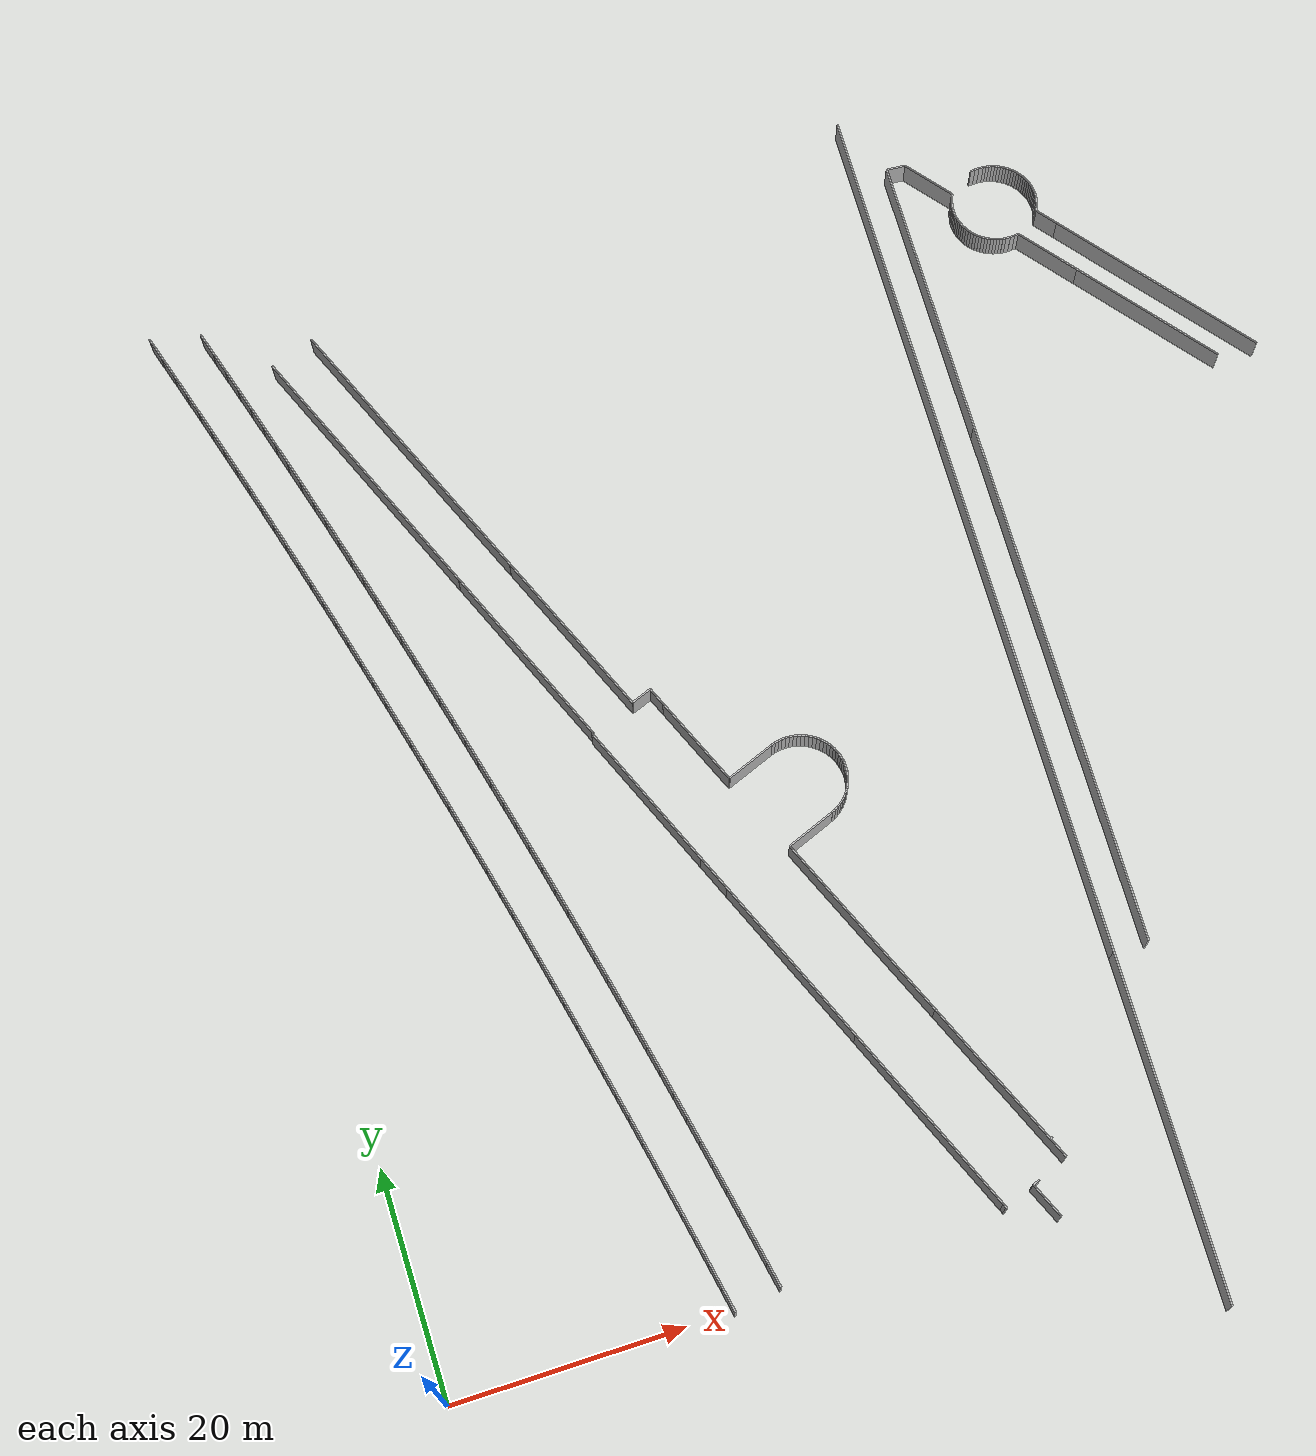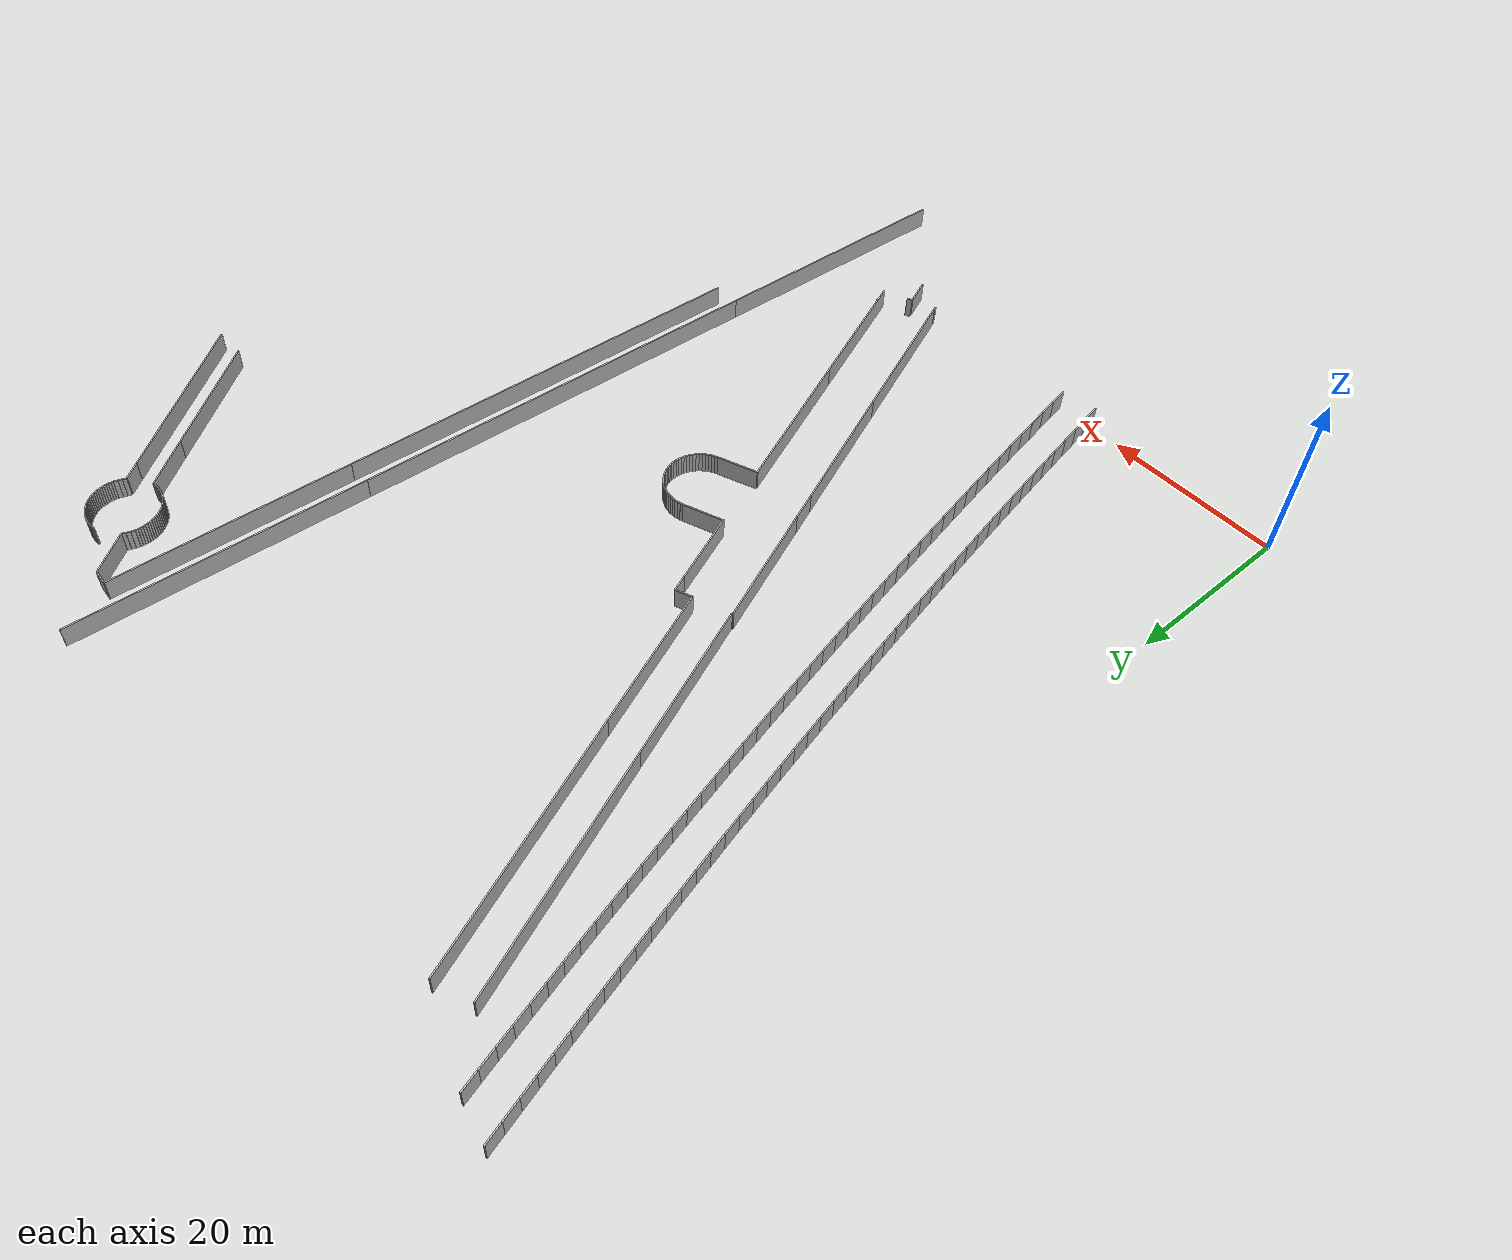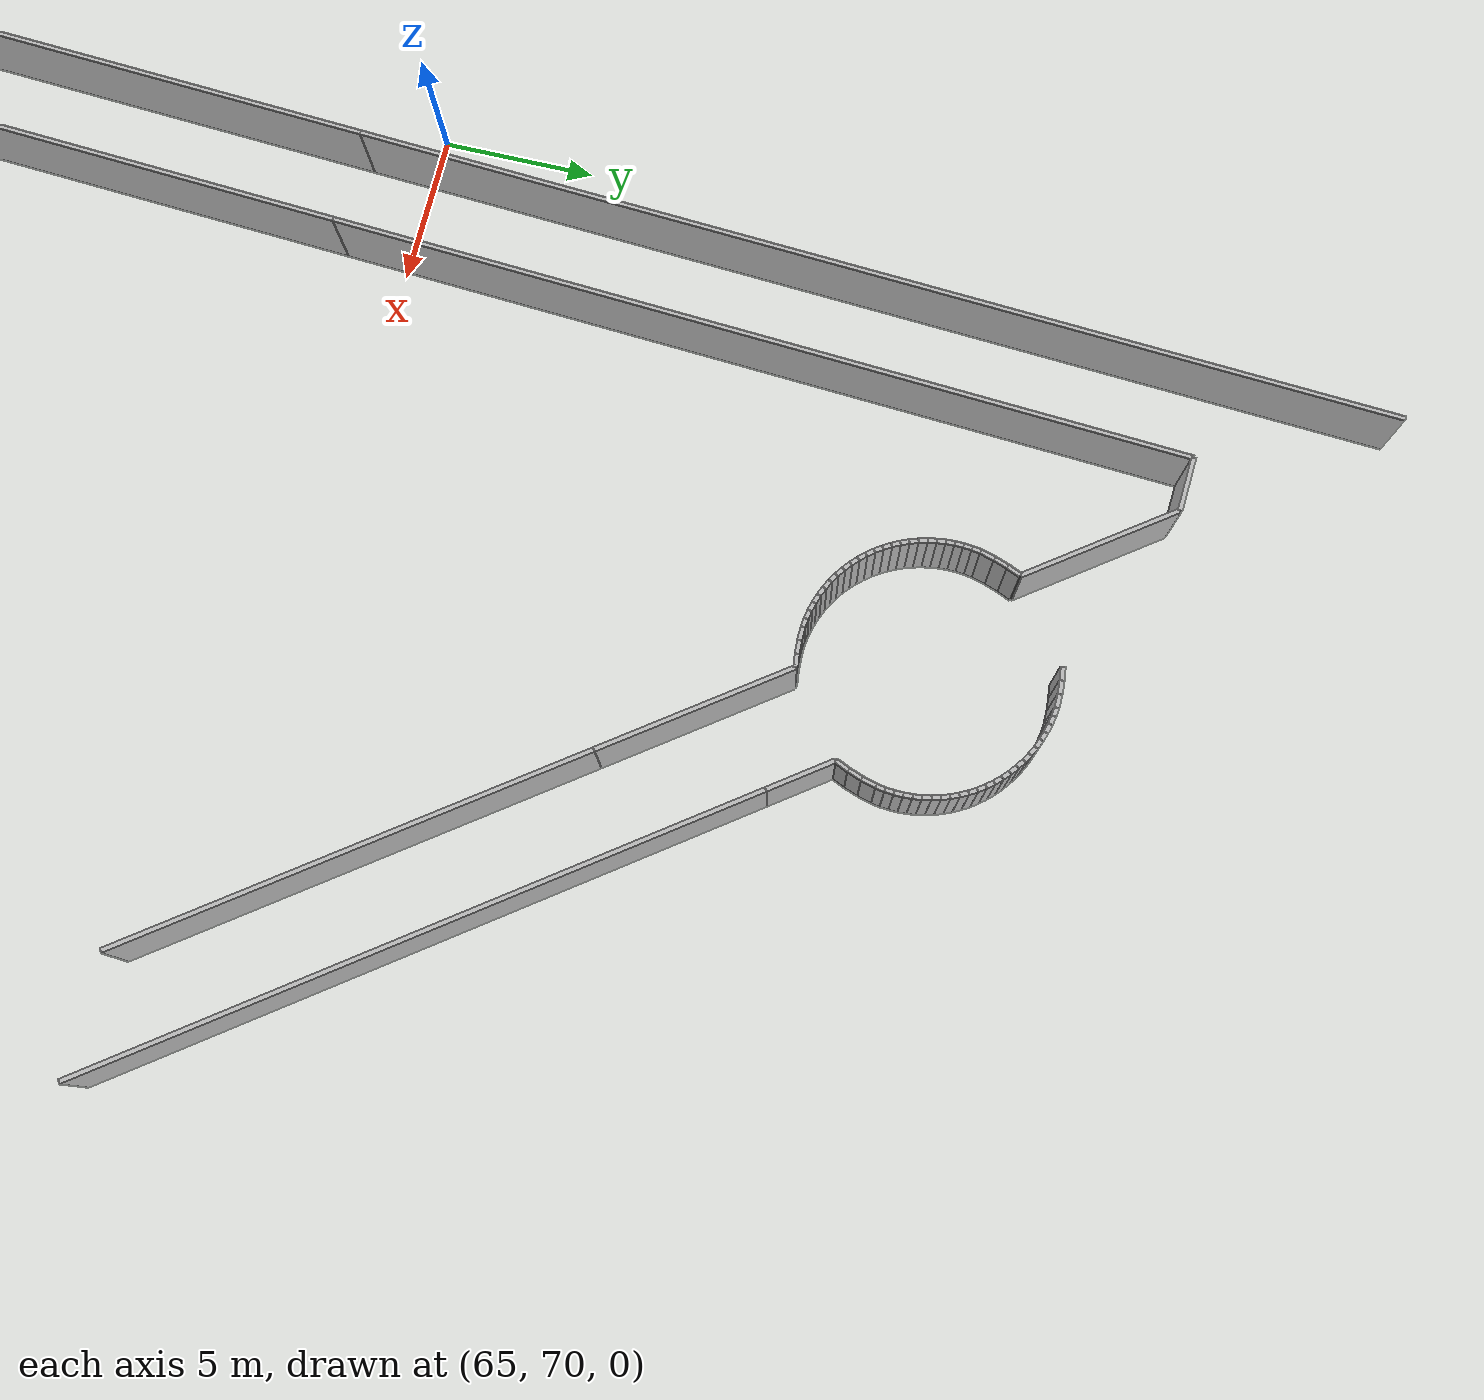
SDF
<?xml version="1.0" ?>
<sdf version="1.6">
  <model name="sps_2314">
    <pose frame="">0 0 0 0 -0 0</pose>
    <static>1</static>
    <self_collide>0</self_collide>
    <allow_auto_disable>0</allow_auto_disable>
    <link name="Wall80">
      <kinematic>0</kinematic>
      <gravity>1</gravity>
      <self_collide>0</self_collide>
      <collision name="collision">
        <geometry>
          <box>
            <size>0.0881448 0.15 2.5</size>
          </box>
        </geometry>
        <pose frame="">0 0 0 0 -0 0</pose>
      </collision>
      <visual name="visual">
        <geometry>
          <box>
            <size>0.0881448 0.15 2.5</size>
          </box>
        </geometry>
        <pose frame="">0 0 0 0 -0 0</pose>
        <cast_shadows>1</cast_shadows>
        <transparency>0.0</transparency>
      </visual>
      <pose frame="">47.404 0.571273 1.25 0 -0 0.37652</pose>
    </link>
    <link name="Wall81">
      <kinematic>0</kinematic>
      <gravity>1</gravity>
      <self_collide>0</self_collide>
      <collision name="collision">
        <geometry>
          <box>
            <size>1.7975 0.15 2.5</size>
          </box>
        </geometry>
        <pose frame="">0 0 0 0 -0 0</pose>
      </collision>
      <visual name="visual">
        <geometry>
          <box>
            <size>1.7975 0.15 2.5</size>
          </box>
        </geometry>
        <pose frame="">0 0 0 0 -0 0</pose>
        <cast_shadows>1</cast_shadows>
        <transparency>0.0</transparency>
      </visual>
      <pose frame="">72.1623 96.0366 1.25 0 0 -0.0584368</pose>
    </link>
    <link name="Wall156">
      <kinematic>0</kinematic>
      <gravity>1</gravity>
      <self_collide>0</self_collide>
      <collision name="collision">
        <geometry>
          <box>
            <size>3.44415 0.15 2.5</size>
          </box>
        </geometry>
        <pose frame="">0 0 0 0 -0 0</pose>
      </collision>
      <visual name="visual">
        <geometry>
          <box>
            <size>3.44415 0.15 2.5</size>
          </box>
        </geometry>
        <pose frame="">0 0 0 0 -0 0</pose>
        <cast_shadows>1</cast_shadows>
        <transparency>0.0</transparency>
      </visual>
      <pose frame="">33.8346 34.9045 1.25 0 0 -1.19321</pose>
    </link>
    <link name="Wall157">
      <kinematic>0</kinematic>
      <gravity>1</gravity>
      <self_collide>0</self_collide>
      <collision name="collision">
        <geometry>
          <box>
            <size>16.5785 0.15 2.5</size>
          </box>
        </geometry>
        <pose frame="">0 0 0 0 -0 0</pose>
      </collision>
      <visual name="visual">
        <geometry>
          <box>
            <size>16.5785 0.15 2.5</size>
          </box>
        </geometry>
        <pose frame="">0 0 0 0 -0 0</pose>
        <cast_shadows>1</cast_shadows>
        <transparency>0.0</transparency>
      </visual>
      <pose frame="">37.5255 25.5984 1.25 0 0 -1.19321</pose>
    </link>
    <link name="Wall158">
      <kinematic>0</kinematic>
      <gravity>1</gravity>
      <self_collide>0</self_collide>
      <collision name="collision">
        <geometry>
          <box>
            <size>18.2175 0.15 2.5</size>
          </box>
        </geometry>
        <pose frame="">0 0 0 0 -0 0</pose>
      </collision>
      <visual name="visual">
        <geometry>
          <box>
            <size>18.2175 0.15 2.5</size>
          </box>
        </geometry>
        <pose frame="">0 0 0 0 -0 0</pose>
        <cast_shadows>1</cast_shadows>
        <transparency>0.0</transparency>
      </visual>
      <pose frame="">43.9397 9.42598 1.25 0 0 -1.19321</pose>
    </link>
    <link name="Wall168">
      <kinematic>0</kinematic>
      <gravity>1</gravity>
      <self_collide>0</self_collide>
      <collision name="collision">
        <geometry>
          <box>
            <size>15.403 0.15 2.5</size>
          </box>
        </geometry>
        <pose frame="">0 0 0 0 -0 0</pose>
      </collision>
      <visual name="visual">
        <geometry>
          <box>
            <size>15.403 0.15 2.5</size>
          </box>
        </geometry>
        <pose frame="">0 0 0 0 -0 0</pose>
        <cast_shadows>1</cast_shadows>
        <transparency>0.0</transparency>
      </visual>
      <pose frame="">89.0073 74.1157 1.25 0 -0 2.20088</pose>
    </link>
    <link name="Wall169">
      <kinematic>0</kinematic>
      <gravity>1</gravity>
      <self_collide>0</self_collide>
      <collision name="collision">
        <geometry>
          <box>
            <size>6.53348 0.15 2.5</size>
          </box>
        </geometry>
        <pose frame="">0 0 0 0 -0 0</pose>
      </collision>
      <visual name="visual">
        <geometry>
          <box>
            <size>6.53348 0.15 2.5</size>
          </box>
        </geometry>
        <pose frame="">0 0 0 0 -0 0</pose>
        <cast_shadows>1</cast_shadows>
        <transparency>0.0</transparency>
      </visual>
      <pose frame="">82.5446 82.9778 1.25 0 -0 2.20088</pose>
    </link>
    <link name="Wall260">
      <kinematic>0</kinematic>
      <gravity>1</gravity>
      <self_collide>0</self_collide>
      <collision name="collision">
        <geometry>
          <box>
            <size>27.9015 0.15 2.5</size>
          </box>
        </geometry>
        <pose frame="">0 0 0 0 -0 0</pose>
      </collision>
      <visual name="visual">
        <geometry>
          <box>
            <size>27.9015 0.15 2.5</size>
          </box>
        </geometry>
        <pose frame="">0 0 0 0 -0 0</pose>
        <cast_shadows>1</cast_shadows>
        <transparency>0.0</transparency>
      </visual>
      <pose frame="">15.7376 80.8615 1.25 0 0 -1.19328</pose>
    </link>
    <link name="Wall261">
      <kinematic>0</kinematic>
      <gravity>1</gravity>
      <self_collide>0</self_collide>
      <collision name="collision">
        <geometry>
          <box>
            <size>18.9599 0.15 2.5</size>
          </box>
        </geometry>
        <pose frame="">0 0 0 0 -0 0</pose>
      </collision>
      <visual name="visual">
        <geometry>
          <box>
            <size>18.9599 0.15 2.5</size>
          </box>
        </geometry>
        <pose frame="">0 0 0 0 -0 0</pose>
        <cast_shadows>1</cast_shadows>
        <transparency>0.0</transparency>
      </visual>
      <pose frame="">24.3744 59.0807 1.25 0 0 -1.19328</pose>
    </link>
    <link name="Wall262">
      <kinematic>0</kinematic>
      <gravity>1</gravity>
      <self_collide>0</self_collide>
      <collision name="collision">
        <geometry>
          <box>
            <size>3.33313 0.15 2.5</size>
          </box>
        </geometry>
        <pose frame="">0 0 0 0 -0 0</pose>
      </collision>
      <visual name="visual">
        <geometry>
          <box>
            <size>3.33313 0.15 2.5</size>
          </box>
        </geometry>
        <pose frame="">0 0 0 0 -0 0</pose>
        <cast_shadows>1</cast_shadows>
        <transparency>0.0</transparency>
      </visual>
      <pose frame="">50.7768 0.116103 1.25 0 0 -1.18645</pose>
    </link>
    <link name="Wall322">
      <kinematic>0</kinematic>
      <gravity>1</gravity>
      <self_collide>0</self_collide>
      <collision name="collision">
        <geometry>
          <box>
            <size>4.74975 0.15 2.5</size>
          </box>
        </geometry>
        <pose frame="">0 0 0 0 -0 0</pose>
      </collision>
      <visual name="visual">
        <geometry>
          <box>
            <size>4.74975 0.15 2.5</size>
          </box>
        </geometry>
        <pose frame="">0 0 0 0 -0 0</pose>
        <cast_shadows>1</cast_shadows>
        <transparency>0.0</transparency>
      </visual>
      <pose frame="">39.9748 43.4954 1.25 0 0 -2.76404</pose>
    </link>
    <link name="Wall323">
      <kinematic>0</kinematic>
      <gravity>1</gravity>
      <self_collide>0</self_collide>
      <collision name="collision">
        <geometry>
          <box>
            <size>0.65133 0.15 2.5</size>
          </box>
        </geometry>
        <pose frame="">0 0 0 0 -0 0</pose>
      </collision>
      <visual name="visual">
        <geometry>
          <box>
            <size>0.65133 0.15 2.5</size>
          </box>
        </geometry>
        <pose frame="">0 0 0 0 -0 0</pose>
        <cast_shadows>1</cast_shadows>
        <transparency>0.0</transparency>
      </visual>
      <pose frame="">50.4546 1.7812 1.25 0 -0 0.377757</pose>
    </link>
    <link name="Wall325">
      <kinematic>0</kinematic>
      <gravity>1</gravity>
      <self_collide>0</self_collide>
      <collision name="collision">
        <geometry>
          <box>
            <size>5.38312 0.15 2.5</size>
          </box>
        </geometry>
        <pose frame="">0 0 0 0 -0 0</pose>
      </collision>
      <visual name="visual">
        <geometry>
          <box>
            <size>5.38312 0.15 2.5</size>
          </box>
        </geometry>
        <pose frame="">0 0 0 0 -0 0</pose>
        <cast_shadows>1</cast_shadows>
        <transparency>0.0</transparency>
      </visual>
      <pose frame="">74.6453 93.8093 1.25 0 0 -0.940765</pose>
    </link>
    <link name="Wall387">
      <kinematic>0</kinematic>
      <gravity>1</gravity>
      <self_collide>0</self_collide>
      <collision name="collision">
        <geometry>
          <box>
            <size>1.81498 0.15 2.5</size>
          </box>
        </geometry>
        <pose frame="">0 0 0 0 -0 0</pose>
      </collision>
      <visual name="visual">
        <geometry>
          <box>
            <size>1.81498 0.15 2.5</size>
          </box>
        </geometry>
        <pose frame="">0 0 0 0 -0 0</pose>
        <cast_shadows>1</cast_shadows>
        <transparency>0.0</transparency>
      </visual>
      <pose frame="">34.1348 51.7776 1.25 0 0 -1.19318</pose>
    </link>
    <link name="Wall388">
      <kinematic>0</kinematic>
      <gravity>1</gravity>
      <self_collide>0</self_collide>
      <collision name="collision">
        <geometry>
          <box>
            <size>8.94427 0.15 2.5</size>
          </box>
        </geometry>
        <pose frame="">0 0 0 0 -0 0</pose>
      </collision>
      <visual name="visual">
        <geometry>
          <box>
            <size>8.94427 0.15 2.5</size>
          </box>
        </geometry>
        <pose frame="">0 0 0 0 -0 0</pose>
        <cast_shadows>1</cast_shadows>
        <transparency>0.0</transparency>
      </visual>
      <pose frame="">36.1183 46.7769 1.25 0 0 -1.19318</pose>
    </link>
    <link name="Wall389">
      <kinematic>0</kinematic>
      <gravity>1</gravity>
      <self_collide>0</self_collide>
      <collision name="collision">
        <geometry>
          <box>
            <size>18.6084 0.15 2.5</size>
          </box>
        </geometry>
        <pose frame="">0 0 0 0 -0 0</pose>
      </collision>
      <visual name="visual">
        <geometry>
          <box>
            <size>18.6084 0.15 2.5</size>
          </box>
        </geometry>
        <pose frame="">0 0 0 0 -0 0</pose>
        <cast_shadows>1</cast_shadows>
        <transparency>0.0</transparency>
      </visual>
      <pose frame="">44.1558 26.5383 1.25 0 0 -1.19216</pose>
    </link>
    <link name="Wall390">
      <kinematic>0</kinematic>
      <gravity>1</gravity>
      <self_collide>0</self_collide>
      <collision name="collision">
        <geometry>
          <box>
            <size>16.0313 0.15 2.5</size>
          </box>
        </geometry>
        <pose frame="">0 0 0 0 -0 0</pose>
      </collision>
      <visual name="visual">
        <geometry>
          <box>
            <size>16.0313 0.15 2.5</size>
          </box>
        </geometry>
        <pose frame="">0 0 0 0 -0 0</pose>
        <cast_shadows>1</cast_shadows>
        <transparency>0.0</transparency>
      </visual>
      <pose frame="">50.5581 10.4452 1.25 0 0 -1.19216</pose>
    </link>
    <link name="Wall401">
      <kinematic>0</kinematic>
      <gravity>1</gravity>
      <self_collide>0</self_collide>
      <collision name="collision">
        <geometry>
          <box>
            <size>21.9145 0.15 2.5</size>
          </box>
        </geometry>
        <pose frame="">0 0 0 0 -0 0</pose>
      </collision>
      <visual name="visual">
        <geometry>
          <box>
            <size>21.9145 0.15 2.5</size>
          </box>
        </geometry>
        <pose frame="">0 0 0 0 -0 0</pose>
        <cast_shadows>1</cast_shadows>
        <transparency>0.0</transparency>
      </visual>
      <pose frame="">90.9256 76.7463 1.25 0 -0 2.20088</pose>
    </link>
    <link name="Wall402">
      <kinematic>0</kinematic>
      <gravity>1</gravity>
      <self_collide>0</self_collide>
      <collision name="collision">
        <geometry>
          <box>
            <size>2.26266 0.15 2.5</size>
          </box>
        </geometry>
        <pose frame="">0 0 0 0 -0 0</pose>
      </collision>
      <visual name="visual">
        <geometry>
          <box>
            <size>2.26266 0.15 2.5</size>
          </box>
        </geometry>
        <pose frame="">0 0 0 0 -0 0</pose>
        <cast_shadows>1</cast_shadows>
        <transparency>0.0</transparency>
      </visual>
      <pose frame="">83.8028 86.5136 1.25 0 -0 2.20088</pose>
    </link>
    <link name="Wall486">
      <kinematic>0</kinematic>
      <gravity>1</gravity>
      <self_collide>0</self_collide>
      <collision name="collision">
        <geometry>
          <box>
            <size>29.6463 0.15 2.5</size>
          </box>
        </geometry>
        <pose frame="">0 0 0 0 -0 0</pose>
      </collision>
      <visual name="visual">
        <geometry>
          <box>
            <size>29.6463 0.15 2.5</size>
          </box>
        </geometry>
        <pose frame="">0 0 0 0 -0 0</pose>
        <cast_shadows>1</cast_shadows>
        <transparency>0.0</transparency>
      </visual>
      <pose frame="">20.1497 81.6725 1.25 0 0 -1.19329</pose>
    </link>
    <link name="Wall487">
      <kinematic>0</kinematic>
      <gravity>1</gravity>
      <self_collide>0</self_collide>
      <collision name="collision">
        <geometry>
          <box>
            <size>17.2147 0.15 2.5</size>
          </box>
        </geometry>
        <pose frame="">0 0 0 0 -0 0</pose>
      </collision>
      <visual name="visual">
        <geometry>
          <box>
            <size>17.2147 0.15 2.5</size>
          </box>
        </geometry>
        <pose frame="">0 0 0 0 -0 0</pose>
        <cast_shadows>1</cast_shadows>
        <transparency>0.0</transparency>
      </visual>
      <pose frame="">28.7862 59.8918 1.25 0 0 -1.19329</pose>
    </link>
    <link name="Wall488">
      <kinematic>0</kinematic>
      <gravity>1</gravity>
      <self_collide>0</self_collide>
      <collision name="collision">
        <geometry>
          <box>
            <size>4.75138 0.15 2.5</size>
          </box>
        </geometry>
        <pose frame="">0 0 0 0 -0 0</pose>
      </collision>
      <visual name="visual">
        <geometry>
          <box>
            <size>4.75138 0.15 2.5</size>
          </box>
        </geometry>
        <pose frame="">0 0 0 0 -0 0</pose>
        <cast_shadows>1</cast_shadows>
        <transparency>0.0</transparency>
      </visual>
      <pose frame="">42.9249 36.0592 1.25 0 -0 0.377513</pose>
    </link>
    <link name="Wall490">
      <kinematic>0</kinematic>
      <gravity>1</gravity>
      <self_collide>0</self_collide>
      <collision name="collision">
        <geometry>
          <box>
            <size>0.233288 0.15 2.5</size>
          </box>
        </geometry>
        <pose frame="">0 0 0 0 -0 0</pose>
      </collision>
      <visual name="visual">
        <geometry>
          <box>
            <size>0.233288 0.15 2.5</size>
          </box>
        </geometry>
        <pose frame="">0 0 0 0 -0 0</pose>
        <cast_shadows>1</cast_shadows>
        <transparency>0.0</transparency>
      </visual>
      <pose frame="">52.8953 4.79307 1.25 0 -0 0.377543</pose>
    </link>
    <link name="Wall585">
      <kinematic>0</kinematic>
      <gravity>1</gravity>
      <self_collide>0</self_collide>
      <collision name="collision">
        <geometry>
          <box>
            <size>14.7591 0.15 2.5</size>
          </box>
        </geometry>
        <pose frame="">0 0 0 0 -0 0</pose>
      </collision>
      <visual name="visual">
        <geometry>
          <box>
            <size>14.7591 0.15 2.5</size>
          </box>
        </geometry>
        <pose frame="">0 0 0 0 -0 0</pose>
        <cast_shadows>1</cast_shadows>
        <transparency>0.0</transparency>
      </visual>
      <pose frame="">30.4788 43.3649 1.25 0 0 -1.19318</pose>
    </link>
    <link name="Wall586">
      <kinematic>0</kinematic>
      <gravity>1</gravity>
      <self_collide>0</self_collide>
      <collision name="collision">
        <geometry>
          <box>
            <size>1.98101 0.15 2.5</size>
          </box>
        </geometry>
        <pose frame="">0 0 0 0 -0 0</pose>
      </collision>
      <visual name="visual">
        <geometry>
          <box>
            <size>1.98101 0.15 2.5</size>
          </box>
        </geometry>
        <pose frame="">0 0 0 0 -0 0</pose>
        <cast_shadows>1</cast_shadows>
        <transparency>0.0</transparency>
      </visual>
      <pose frame="">32.8796 52.2558 1.25 0 -0 0.377714</pose>
    </link>
    <link name="Wall587">
      <kinematic>0</kinematic>
      <gravity>1</gravity>
      <self_collide>0</self_collide>
      <collision name="collision">
        <geometry>
          <box>
            <size>0.39949 0.15 2.5</size>
          </box>
        </geometry>
        <pose frame="">0 0 0 0 -0 0</pose>
      </collision>
      <visual name="visual">
        <geometry>
          <box>
            <size>0.39949 0.15 2.5</size>
          </box>
        </geometry>
        <pose frame="">0 0 0 0 -0 0</pose>
        <cast_shadows>1</cast_shadows>
        <transparency>0.0</transparency>
      </visual>
      <pose frame="">47.3715 0.773177 1.25 0 0 -1.19355</pose>
    </link>
    <link name="Wall588">
      <kinematic>0</kinematic>
      <gravity>1</gravity>
      <self_collide>0</self_collide>
      <collision name="collision">
        <geometry>
          <box>
            <size>34.4283 0.15 2.5</size>
          </box>
        </geometry>
        <pose frame="">0 0 0 0 -0 0</pose>
      </collision>
      <visual name="visual">
        <geometry>
          <box>
            <size>34.4283 0.15 2.5</size>
          </box>
        </geometry>
        <pose frame="">0 0 0 0 -0 0</pose>
        <cast_shadows>1</cast_shadows>
        <transparency>0.0</transparency>
      </visual>
      <pose frame="">67.4748 85.0778 1.25 0 0 -1.62928</pose>
    </link>
    <link name="Wall589">
      <kinematic>0</kinematic>
      <gravity>1</gravity>
      <self_collide>0</self_collide>
      <collision name="collision">
        <geometry>
          <box>
            <size>50.0856 0.15 2.5</size>
          </box>
        </geometry>
        <pose frame="">0 0 0 0 -0 0</pose>
      </collision>
      <visual name="visual">
        <geometry>
          <box>
            <size>50.0856 0.15 2.5</size>
          </box>
        </geometry>
        <pose frame="">0 0 0 0 -0 0</pose>
        <cast_shadows>1</cast_shadows>
        <transparency>0.0</transparency>
      </visual>
      <pose frame="">65.0047 42.8931 1.25 0 0 -1.62928</pose>
    </link>
    <link name="Wall590">
      <kinematic>0</kinematic>
      <gravity>1</gravity>
      <self_collide>0</self_collide>
      <collision name="collision">
        <geometry>
          <box>
            <size>30.3164 0.15 2.5</size>
          </box>
        </geometry>
        <pose frame="">0 0 0 0 -0 0</pose>
      </collision>
      <visual name="visual">
        <geometry>
          <box>
            <size>30.3164 0.15 2.5</size>
          </box>
        </geometry>
        <pose frame="">0 0 0 0 -0 0</pose>
        <cast_shadows>1</cast_shadows>
        <transparency>0.0</transparency>
      </visual>
      <pose frame="">62.6547 2.76079 1.25 0 0 -1.62928</pose>
    </link>
    <link name="Wall663">
      <kinematic>0</kinematic>
      <gravity>1</gravity>
      <self_collide>0</self_collide>
      <collision name="collision">
        <geometry>
          <box>
            <size>0.119337 0.15 2.5</size>
          </box>
        </geometry>
        <pose frame="">0 0 0 0 -0 0</pose>
      </collision>
      <visual name="visual">
        <geometry>
          <box>
            <size>0.119337 0.15 2.5</size>
          </box>
        </geometry>
        <pose frame="">0 0 0 0 -0 0</pose>
        <cast_shadows>1</cast_shadows>
        <transparency>0.0</transparency>
      </visual>
      <pose frame="">27.8133 50.2464 1.25 0 -0 0.375473</pose>
    </link>
    <link name="Wall667">
      <kinematic>0</kinematic>
      <gravity>1</gravity>
      <self_collide>0</self_collide>
      <collision name="collision">
        <geometry>
          <box>
            <size>28.2443 0.15 2.5</size>
          </box>
        </geometry>
        <pose frame="">0 0 0 0 -0 0</pose>
      </collision>
      <visual name="visual">
        <geometry>
          <box>
            <size>28.2443 0.15 2.5</size>
          </box>
        </geometry>
        <pose frame="">0 0 0 0 -0 0</pose>
        <cast_shadows>1</cast_shadows>
        <transparency>0.0</transparency>
      </visual>
      <pose frame="">70.4395 81.9911 1.25 0 0 -1.62929</pose>
    </link>
    <link name="Wall668">
      <kinematic>0</kinematic>
      <gravity>1</gravity>
      <self_collide>0</self_collide>
      <collision name="collision">
        <geometry>
          <box>
            <size>50.0856 0.15 2.5</size>
          </box>
        </geometry>
        <pose frame="">0 0 0 0 -0 0</pose>
      </collision>
      <visual name="visual">
        <geometry>
          <box>
            <size>50.0856 0.15 2.5</size>
          </box>
        </geometry>
        <pose frame="">0 0 0 0 -0 0</pose>
        <cast_shadows>1</cast_shadows>
        <transparency>0.0</transparency>
      </visual>
      <pose frame="">68.1501 42.8931 1.25 0 0 -1.62929</pose>
    </link>
    <link name="Wall4661">
      <kinematic>0</kinematic>
      <gravity>1</gravity>
      <self_collide>0</self_collide>
      <collision name="collision">
        <geometry>
          <box>
            <size>2.25472 0.15 2.5</size>
          </box>
        </geometry>
        <pose frame="">0 0 0 0 -0 0</pose>
      </collision>
      <visual name="visual">
        <geometry>
          <box>
            <size>2.25472 0.15 2.5</size>
          </box>
        </geometry>
        <pose frame="">0 0 0 0 -0 0</pose>
        <cast_shadows>1</cast_shadows>
        <transparency>0.0</transparency>
      </visual>
      <pose frame="">27.8527 1.40709 1.25 0 -0 1.74643</pose>
    </link>
    <link name="Wall4662">
      <kinematic>0</kinematic>
      <gravity>1</gravity>
      <self_collide>0</self_collide>
      <collision name="collision">
        <geometry>
          <box>
            <size>2.25462 0.15 2.5</size>
          </box>
        </geometry>
        <pose frame="">0 0 0 0 -0 0</pose>
      </collision>
      <visual name="visual">
        <geometry>
          <box>
            <size>2.25462 0.15 2.5</size>
          </box>
        </geometry>
        <pose frame="">0 0 0 0 -0 0</pose>
        <cast_shadows>1</cast_shadows>
        <transparency>0.0</transparency>
      </visual>
      <pose frame="">27.456 3.6266 1.25 0 -0 1.74881</pose>
    </link>
    <link name="Wall4663">
      <kinematic>0</kinematic>
      <gravity>1</gravity>
      <self_collide>0</self_collide>
      <collision name="collision">
        <geometry>
          <box>
            <size>2.25462 0.15 2.5</size>
          </box>
        </geometry>
        <pose frame="">0 0 0 0 -0 0</pose>
      </collision>
      <visual name="visual">
        <geometry>
          <box>
            <size>2.25462 0.15 2.5</size>
          </box>
        </geometry>
        <pose frame="">0 0 0 0 -0 0</pose>
        <cast_shadows>1</cast_shadows>
        <transparency>0.0</transparency>
      </visual>
      <pose frame="">27.0541 5.84511 1.25 0 -0 1.75123</pose>
    </link>
    <link name="Wall4664">
      <kinematic>0</kinematic>
      <gravity>1</gravity>
      <self_collide>0</self_collide>
      <collision name="collision">
        <geometry>
          <box>
            <size>2.25472 0.15 2.5</size>
          </box>
        </geometry>
        <pose frame="">0 0 0 0 -0 0</pose>
      </collision>
      <visual name="visual">
        <geometry>
          <box>
            <size>2.25472 0.15 2.5</size>
          </box>
        </geometry>
        <pose frame="">0 0 0 0 -0 0</pose>
        <cast_shadows>1</cast_shadows>
        <transparency>0.0</transparency>
      </visual>
      <pose frame="">26.6469 8.0627 1.25 0 -0 1.75356</pose>
    </link>
    <link name="Wall4665">
      <kinematic>0</kinematic>
      <gravity>1</gravity>
      <self_collide>0</self_collide>
      <collision name="collision">
        <geometry>
          <box>
            <size>2.25452 0.15 2.5</size>
          </box>
        </geometry>
        <pose frame="">0 0 0 0 -0 0</pose>
      </collision>
      <visual name="visual">
        <geometry>
          <box>
            <size>2.25452 0.15 2.5</size>
          </box>
        </geometry>
        <pose frame="">0 0 0 0 -0 0</pose>
        <cast_shadows>1</cast_shadows>
        <transparency>0.0</transparency>
      </visual>
      <pose frame="">26.2345 10.2793 1.25 0 -0 1.75592</pose>
    </link>
    <link name="Wall4666">
      <kinematic>0</kinematic>
      <gravity>1</gravity>
      <self_collide>0</self_collide>
      <collision name="collision">
        <geometry>
          <box>
            <size>2.25475 0.15 2.5</size>
          </box>
        </geometry>
        <pose frame="">0 0 0 0 -0 0</pose>
      </collision>
      <visual name="visual">
        <geometry>
          <box>
            <size>2.25475 0.15 2.5</size>
          </box>
        </geometry>
        <pose frame="">0 0 0 0 -0 0</pose>
        <cast_shadows>1</cast_shadows>
        <transparency>0.0</transparency>
      </visual>
      <pose frame="">25.8169 12.4949 1.25 0 -0 1.75835</pose>
    </link>
    <link name="Wall4667">
      <kinematic>0</kinematic>
      <gravity>1</gravity>
      <self_collide>0</self_collide>
      <collision name="collision">
        <geometry>
          <box>
            <size>2.25399 0.15 2.5</size>
          </box>
        </geometry>
        <pose frame="">0 0 0 0 -0 0</pose>
      </collision>
      <visual name="visual">
        <geometry>
          <box>
            <size>2.25399 0.15 2.5</size>
          </box>
        </geometry>
        <pose frame="">0 0 0 0 -0 0</pose>
        <cast_shadows>1</cast_shadows>
        <transparency>0.0</transparency>
      </visual>
      <pose frame="">25.3937 14.7092 1.25 0 -0 1.76092</pose>
    </link>
    <link name="Wall4668">
      <kinematic>0</kinematic>
      <gravity>1</gravity>
      <self_collide>0</self_collide>
      <collision name="collision">
        <geometry>
          <box>
            <size>2.2547 0.15 2.5</size>
          </box>
        </geometry>
        <pose frame="">0 0 0 0 -0 0</pose>
      </collision>
      <visual name="visual">
        <geometry>
          <box>
            <size>2.2547 0.15 2.5</size>
          </box>
        </geometry>
        <pose frame="">0 0 0 0 -0 0</pose>
        <cast_shadows>1</cast_shadows>
        <transparency>0.0</transparency>
      </visual>
      <pose frame="">24.9654 16.9225 1.25 0 -0 1.76296</pose>
    </link>
    <link name="Wall4669">
      <kinematic>0</kinematic>
      <gravity>1</gravity>
      <self_collide>0</self_collide>
      <collision name="collision">
        <geometry>
          <box>
            <size>2.2546 0.15 2.5</size>
          </box>
        </geometry>
        <pose frame="">0 0 0 0 -0 0</pose>
      </collision>
      <visual name="visual">
        <geometry>
          <box>
            <size>2.2546 0.15 2.5</size>
          </box>
        </geometry>
        <pose frame="">0 0 0 0 -0 0</pose>
        <cast_shadows>1</cast_shadows>
        <transparency>0.0</transparency>
      </visual>
      <pose frame="">24.5321 19.1351 1.25 0 -0 1.76542</pose>
    </link>
    <link name="Wall4670">
      <kinematic>0</kinematic>
      <gravity>1</gravity>
      <self_collide>0</self_collide>
      <collision name="collision">
        <geometry>
          <box>
            <size>2.25467 0.15 2.5</size>
          </box>
        </geometry>
        <pose frame="">0 0 0 0 -0 0</pose>
      </collision>
      <visual name="visual">
        <geometry>
          <box>
            <size>2.25467 0.15 2.5</size>
          </box>
        </geometry>
        <pose frame="">0 0 0 0 -0 0</pose>
        <cast_shadows>1</cast_shadows>
        <transparency>0.0</transparency>
      </visual>
      <pose frame="">24.0933 21.3466 1.25 0 -0 1.76793</pose>
    </link>
    <link name="Wall4671">
      <kinematic>0</kinematic>
      <gravity>1</gravity>
      <self_collide>0</self_collide>
      <collision name="collision">
        <geometry>
          <box>
            <size>2.25445 0.15 2.5</size>
          </box>
        </geometry>
        <pose frame="">0 0 0 0 -0 0</pose>
      </collision>
      <visual name="visual">
        <geometry>
          <box>
            <size>2.25445 0.15 2.5</size>
          </box>
        </geometry>
        <pose frame="">0 0 0 0 -0 0</pose>
        <cast_shadows>1</cast_shadows>
        <transparency>0.0</transparency>
      </visual>
      <pose frame="">23.6492 23.557 1.25 0 -0 1.77021</pose>
    </link>
    <link name="Wall4672">
      <kinematic>0</kinematic>
      <gravity>1</gravity>
      <self_collide>0</self_collide>
      <collision name="collision">
        <geometry>
          <box>
            <size>2.25471 0.15 2.5</size>
          </box>
        </geometry>
        <pose frame="">0 0 0 0 -0 0</pose>
      </collision>
      <visual name="visual">
        <geometry>
          <box>
            <size>2.25471 0.15 2.5</size>
          </box>
        </geometry>
        <pose frame="">0 0 0 0 -0 0</pose>
        <cast_shadows>1</cast_shadows>
        <transparency>0.0</transparency>
      </visual>
      <pose frame="">23.2 25.7664 1.25 0 -0 1.77253</pose>
    </link>
    <link name="Wall4673">
      <kinematic>0</kinematic>
      <gravity>1</gravity>
      <self_collide>0</self_collide>
      <collision name="collision">
        <geometry>
          <box>
            <size>2.25463 0.15 2.5</size>
          </box>
        </geometry>
        <pose frame="">0 0 0 0 -0 0</pose>
      </collision>
      <visual name="visual">
        <geometry>
          <box>
            <size>2.25463 0.15 2.5</size>
          </box>
        </geometry>
        <pose frame="">0 0 0 0 -0 0</pose>
        <cast_shadows>1</cast_shadows>
        <transparency>0.0</transparency>
      </visual>
      <pose frame="">22.7456 27.9748 1.25 0 -0 1.77492</pose>
    </link>
    <link name="Wall4674">
      <kinematic>0</kinematic>
      <gravity>1</gravity>
      <self_collide>0</self_collide>
      <collision name="collision">
        <geometry>
          <box>
            <size>2.25471 0.15 2.5</size>
          </box>
        </geometry>
        <pose frame="">0 0 0 0 -0 0</pose>
      </collision>
      <visual name="visual">
        <geometry>
          <box>
            <size>2.25471 0.15 2.5</size>
          </box>
        </geometry>
        <pose frame="">0 0 0 0 -0 0</pose>
        <cast_shadows>1</cast_shadows>
        <transparency>0.0</transparency>
      </visual>
      <pose frame="">22.2858 30.1821 1.25 0 -0 1.77734</pose>
    </link>
    <link name="Wall4675">
      <kinematic>0</kinematic>
      <gravity>1</gravity>
      <self_collide>0</self_collide>
      <collision name="collision">
        <geometry>
          <box>
            <size>2.25465 0.15 2.5</size>
          </box>
        </geometry>
        <pose frame="">0 0 0 0 -0 0</pose>
      </collision>
      <visual name="visual">
        <geometry>
          <box>
            <size>2.25465 0.15 2.5</size>
          </box>
        </geometry>
        <pose frame="">0 0 0 0 -0 0</pose>
        <cast_shadows>1</cast_shadows>
        <transparency>0.0</transparency>
      </visual>
      <pose frame="">21.8209 32.3883 1.25 0 -0 1.7797</pose>
    </link>
    <link name="Wall4676">
      <kinematic>0</kinematic>
      <gravity>1</gravity>
      <self_collide>0</self_collide>
      <collision name="collision">
        <geometry>
          <box>
            <size>2.25454 0.15 2.5</size>
          </box>
        </geometry>
        <pose frame="">0 0 0 0 -0 0</pose>
      </collision>
      <visual name="visual">
        <geometry>
          <box>
            <size>2.25454 0.15 2.5</size>
          </box>
        </geometry>
        <pose frame="">0 0 0 0 -0 0</pose>
        <cast_shadows>1</cast_shadows>
        <transparency>0.0</transparency>
      </visual>
      <pose frame="">21.3507 34.5933 1.25 0 -0 1.78207</pose>
    </link>
    <link name="Wall4677">
      <kinematic>0</kinematic>
      <gravity>1</gravity>
      <self_collide>0</self_collide>
      <collision name="collision">
        <geometry>
          <box>
            <size>2.25467 0.15 2.5</size>
          </box>
        </geometry>
        <pose frame="">0 0 0 0 -0 0</pose>
      </collision>
      <visual name="visual">
        <geometry>
          <box>
            <size>2.25467 0.15 2.5</size>
          </box>
        </geometry>
        <pose frame="">0 0 0 0 -0 0</pose>
        <cast_shadows>1</cast_shadows>
        <transparency>0.0</transparency>
      </visual>
      <pose frame="">20.8752 36.7972 1.25 0 -0 1.78452</pose>
    </link>
    <link name="Wall4678">
      <kinematic>0</kinematic>
      <gravity>1</gravity>
      <self_collide>0</self_collide>
      <collision name="collision">
        <geometry>
          <box>
            <size>2.25482 0.15 2.5</size>
          </box>
        </geometry>
        <pose frame="">0 0 0 0 -0 0</pose>
      </collision>
      <visual name="visual">
        <geometry>
          <box>
            <size>2.25482 0.15 2.5</size>
          </box>
        </geometry>
        <pose frame="">0 0 0 0 -0 0</pose>
        <cast_shadows>1</cast_shadows>
        <transparency>0.0</transparency>
      </visual>
      <pose frame="">20.3944 39.0001 1.25 0 -0 1.78686</pose>
    </link>
    <link name="Wall4679">
      <kinematic>0</kinematic>
      <gravity>1</gravity>
      <self_collide>0</self_collide>
      <collision name="collision">
        <geometry>
          <box>
            <size>2.25435 0.15 2.5</size>
          </box>
        </geometry>
        <pose frame="">0 0 0 0 -0 0</pose>
      </collision>
      <visual name="visual">
        <geometry>
          <box>
            <size>2.25435 0.15 2.5</size>
          </box>
        </geometry>
        <pose frame="">0 0 0 0 -0 0</pose>
        <cast_shadows>1</cast_shadows>
        <transparency>0.0</transparency>
      </visual>
      <pose frame="">19.9085 41.2017 1.25 0 -0 1.78918</pose>
    </link>
    <link name="Wall4680">
      <kinematic>0</kinematic>
      <gravity>1</gravity>
      <self_collide>0</self_collide>
      <collision name="collision">
        <geometry>
          <box>
            <size>2.25458 0.15 2.5</size>
          </box>
        </geometry>
        <pose frame="">0 0 0 0 -0 0</pose>
      </collision>
      <visual name="visual">
        <geometry>
          <box>
            <size>2.25458 0.15 2.5</size>
          </box>
        </geometry>
        <pose frame="">0 0 0 0 -0 0</pose>
        <cast_shadows>1</cast_shadows>
        <transparency>0.0</transparency>
      </visual>
      <pose frame="">19.4174 43.402 1.25 0 -0 1.79162</pose>
    </link>
    <link name="Wall4681">
      <kinematic>0</kinematic>
      <gravity>1</gravity>
      <self_collide>0</self_collide>
      <collision name="collision">
        <geometry>
          <box>
            <size>2.25469 0.15 2.5</size>
          </box>
        </geometry>
        <pose frame="">0 0 0 0 -0 0</pose>
      </collision>
      <visual name="visual">
        <geometry>
          <box>
            <size>2.25469 0.15 2.5</size>
          </box>
        </geometry>
        <pose frame="">0 0 0 0 -0 0</pose>
        <cast_shadows>1</cast_shadows>
        <transparency>0.0</transparency>
      </visual>
      <pose frame="">18.921 45.6013 1.25 0 -0 1.79394</pose>
    </link>
    <link name="Wall4682">
      <kinematic>0</kinematic>
      <gravity>1</gravity>
      <self_collide>0</self_collide>
      <collision name="collision">
        <geometry>
          <box>
            <size>2.25436 0.15 2.5</size>
          </box>
        </geometry>
        <pose frame="">0 0 0 0 -0 0</pose>
      </collision>
      <visual name="visual">
        <geometry>
          <box>
            <size>2.25436 0.15 2.5</size>
          </box>
        </geometry>
        <pose frame="">0 0 0 0 -0 0</pose>
        <cast_shadows>1</cast_shadows>
        <transparency>0.0</transparency>
      </visual>
      <pose frame="">18.4193 47.7993 1.25 0 -0 1.79645</pose>
    </link>
    <link name="Wall4683">
      <kinematic>0</kinematic>
      <gravity>1</gravity>
      <self_collide>0</self_collide>
      <collision name="collision">
        <geometry>
          <box>
            <size>2.25453 0.15 2.5</size>
          </box>
        </geometry>
        <pose frame="">0 0 0 0 -0 0</pose>
      </collision>
      <visual name="visual">
        <geometry>
          <box>
            <size>2.25453 0.15 2.5</size>
          </box>
        </geometry>
        <pose frame="">0 0 0 0 -0 0</pose>
        <cast_shadows>1</cast_shadows>
        <transparency>0.0</transparency>
      </visual>
      <pose frame="">17.9123 49.996 1.25 0 -0 1.79882</pose>
    </link>
    <link name="Wall4684">
      <kinematic>0</kinematic>
      <gravity>1</gravity>
      <self_collide>0</self_collide>
      <collision name="collision">
        <geometry>
          <box>
            <size>2.25472 0.15 2.5</size>
          </box>
        </geometry>
        <pose frame="">0 0 0 0 -0 0</pose>
      </collision>
      <visual name="visual">
        <geometry>
          <box>
            <size>2.25472 0.15 2.5</size>
          </box>
        </geometry>
        <pose frame="">0 0 0 0 -0 0</pose>
        <cast_shadows>1</cast_shadows>
        <transparency>0.0</transparency>
      </visual>
      <pose frame="">17.4002 52.1917 1.25 0 -0 1.80097</pose>
    </link>
    <link name="Wall4685">
      <kinematic>0</kinematic>
      <gravity>1</gravity>
      <self_collide>0</self_collide>
      <collision name="collision">
        <geometry>
          <box>
            <size>2.25456 0.15 2.5</size>
          </box>
        </geometry>
        <pose frame="">0 0 0 0 -0 0</pose>
      </collision>
      <visual name="visual">
        <geometry>
          <box>
            <size>2.25456 0.15 2.5</size>
          </box>
        </geometry>
        <pose frame="">0 0 0 0 -0 0</pose>
        <cast_shadows>1</cast_shadows>
        <transparency>0.0</transparency>
      </visual>
      <pose frame="">16.883 54.3862 1.25 0 -0 1.80352</pose>
    </link>
    <link name="Wall4686">
      <kinematic>0</kinematic>
      <gravity>1</gravity>
      <self_collide>0</self_collide>
      <collision name="collision">
        <geometry>
          <box>
            <size>2.25455 0.15 2.5</size>
          </box>
        </geometry>
        <pose frame="">0 0 0 0 -0 0</pose>
      </collision>
      <visual name="visual">
        <geometry>
          <box>
            <size>2.25455 0.15 2.5</size>
          </box>
        </geometry>
        <pose frame="">0 0 0 0 -0 0</pose>
        <cast_shadows>1</cast_shadows>
        <transparency>0.0</transparency>
      </visual>
      <pose frame="">16.3606 56.5794 1.25 0 -0 1.80583</pose>
    </link>
    <link name="Wall4687">
      <kinematic>0</kinematic>
      <gravity>1</gravity>
      <self_collide>0</self_collide>
      <collision name="collision">
        <geometry>
          <box>
            <size>2.25468 0.15 2.5</size>
          </box>
        </geometry>
        <pose frame="">0 0 0 0 -0 0</pose>
      </collision>
      <visual name="visual">
        <geometry>
          <box>
            <size>2.25468 0.15 2.5</size>
          </box>
        </geometry>
        <pose frame="">0 0 0 0 -0 0</pose>
        <cast_shadows>1</cast_shadows>
        <transparency>0.0</transparency>
      </visual>
      <pose frame="">15.8328 58.7714 1.25 0 -0 1.80826</pose>
    </link>
    <link name="Wall4688">
      <kinematic>0</kinematic>
      <gravity>1</gravity>
      <self_collide>0</self_collide>
      <collision name="collision">
        <geometry>
          <box>
            <size>2.25468 0.15 2.5</size>
          </box>
        </geometry>
        <pose frame="">0 0 0 0 -0 0</pose>
      </collision>
      <visual name="visual">
        <geometry>
          <box>
            <size>2.25468 0.15 2.5</size>
          </box>
        </geometry>
        <pose frame="">0 0 0 0 -0 0</pose>
        <cast_shadows>1</cast_shadows>
        <transparency>0.0</transparency>
      </visual>
      <pose frame="">15.2999 60.9622 1.25 0 -0 1.81055</pose>
    </link>
    <link name="Wall4689">
      <kinematic>0</kinematic>
      <gravity>1</gravity>
      <self_collide>0</self_collide>
      <collision name="collision">
        <geometry>
          <box>
            <size>2.25465 0.15 2.5</size>
          </box>
        </geometry>
        <pose frame="">0 0 0 0 -0 0</pose>
      </collision>
      <visual name="visual">
        <geometry>
          <box>
            <size>2.25465 0.15 2.5</size>
          </box>
        </geometry>
        <pose frame="">0 0 0 0 -0 0</pose>
        <cast_shadows>1</cast_shadows>
        <transparency>0.0</transparency>
      </visual>
      <pose frame="">14.7619 63.1517 1.25 0 -0 1.813</pose>
    </link>
    <link name="Wall4690">
      <kinematic>0</kinematic>
      <gravity>1</gravity>
      <self_collide>0</self_collide>
      <collision name="collision">
        <geometry>
          <box>
            <size>2.25445 0.15 2.5</size>
          </box>
        </geometry>
        <pose frame="">0 0 0 0 -0 0</pose>
      </collision>
      <visual name="visual">
        <geometry>
          <box>
            <size>2.25445 0.15 2.5</size>
          </box>
        </geometry>
        <pose frame="">0 0 0 0 -0 0</pose>
        <cast_shadows>1</cast_shadows>
        <transparency>0.0</transparency>
      </visual>
      <pose frame="">14.2186 65.3398 1.25 0 -0 1.81534</pose>
    </link>
    <link name="Wall4691">
      <kinematic>0</kinematic>
      <gravity>1</gravity>
      <self_collide>0</self_collide>
      <collision name="collision">
        <geometry>
          <box>
            <size>2.25475 0.15 2.5</size>
          </box>
        </geometry>
        <pose frame="">0 0 0 0 -0 0</pose>
      </collision>
      <visual name="visual">
        <geometry>
          <box>
            <size>2.25475 0.15 2.5</size>
          </box>
        </geometry>
        <pose frame="">0 0 0 0 -0 0</pose>
        <cast_shadows>1</cast_shadows>
        <transparency>0.0</transparency>
      </visual>
      <pose frame="">13.6702 67.5267 1.25 0 -0 1.81765</pose>
    </link>
    <link name="Wall4692">
      <kinematic>0</kinematic>
      <gravity>1</gravity>
      <self_collide>0</self_collide>
      <collision name="collision">
        <geometry>
          <box>
            <size>2.25455 0.15 2.5</size>
          </box>
        </geometry>
        <pose frame="">0 0 0 0 -0 0</pose>
      </collision>
      <visual name="visual">
        <geometry>
          <box>
            <size>2.25455 0.15 2.5</size>
          </box>
        </geometry>
        <pose frame="">0 0 0 0 -0 0</pose>
        <cast_shadows>1</cast_shadows>
        <transparency>0.0</transparency>
      </visual>
      <pose frame="">13.1165 69.7123 1.25 0 -0 1.82016</pose>
    </link>
    <link name="Wall4693">
      <kinematic>0</kinematic>
      <gravity>1</gravity>
      <self_collide>0</self_collide>
      <collision name="collision">
        <geometry>
          <box>
            <size>2.25461 0.15 2.5</size>
          </box>
        </geometry>
        <pose frame="">0 0 0 0 -0 0</pose>
      </collision>
      <visual name="visual">
        <geometry>
          <box>
            <size>2.25461 0.15 2.5</size>
          </box>
        </geometry>
        <pose frame="">0 0 0 0 -0 0</pose>
        <cast_shadows>1</cast_shadows>
        <transparency>0.0</transparency>
      </visual>
      <pose frame="">12.5576 71.8965 1.25 0 -0 1.82245</pose>
    </link>
    <link name="Wall4694">
      <kinematic>0</kinematic>
      <gravity>1</gravity>
      <self_collide>0</self_collide>
      <collision name="collision">
        <geometry>
          <box>
            <size>2.25478 0.15 2.5</size>
          </box>
        </geometry>
        <pose frame="">0 0 0 0 -0 0</pose>
      </collision>
      <visual name="visual">
        <geometry>
          <box>
            <size>2.25478 0.15 2.5</size>
          </box>
        </geometry>
        <pose frame="">0 0 0 0 -0 0</pose>
        <cast_shadows>1</cast_shadows>
        <transparency>0.0</transparency>
      </visual>
      <pose frame="">11.9935 74.0795 1.25 0 -0 1.82491</pose>
    </link>
    <link name="Wall4695">
      <kinematic>0</kinematic>
      <gravity>1</gravity>
      <self_collide>0</self_collide>
      <collision name="collision">
        <geometry>
          <box>
            <size>2.25456 0.15 2.5</size>
          </box>
        </geometry>
        <pose frame="">0 0 0 0 -0 0</pose>
      </collision>
      <visual name="visual">
        <geometry>
          <box>
            <size>2.25456 0.15 2.5</size>
          </box>
        </geometry>
        <pose frame="">0 0 0 0 -0 0</pose>
        <cast_shadows>1</cast_shadows>
        <transparency>0.0</transparency>
      </visual>
      <pose frame="">11.4242 76.2611 1.25 0 -0 1.82721</pose>
    </link>
    <link name="Wall4696">
      <kinematic>0</kinematic>
      <gravity>1</gravity>
      <self_collide>0</self_collide>
      <collision name="collision">
        <geometry>
          <box>
            <size>2.25448 0.15 2.5</size>
          </box>
        </geometry>
        <pose frame="">0 0 0 0 -0 0</pose>
      </collision>
      <visual name="visual">
        <geometry>
          <box>
            <size>2.25448 0.15 2.5</size>
          </box>
        </geometry>
        <pose frame="">0 0 0 0 -0 0</pose>
        <cast_shadows>1</cast_shadows>
        <transparency>0.0</transparency>
      </visual>
      <pose frame="">10.8498 78.4412 1.25 0 -0 1.82962</pose>
    </link>
    <link name="Wall4697">
      <kinematic>0</kinematic>
      <gravity>1</gravity>
      <self_collide>0</self_collide>
      <collision name="collision">
        <geometry>
          <box>
            <size>2.25455 0.15 2.5</size>
          </box>
        </geometry>
        <pose frame="">0 0 0 0 -0 0</pose>
      </collision>
      <visual name="visual">
        <geometry>
          <box>
            <size>2.25455 0.15 2.5</size>
          </box>
        </geometry>
        <pose frame="">0 0 0 0 -0 0</pose>
        <cast_shadows>1</cast_shadows>
        <transparency>0.0</transparency>
      </visual>
      <pose frame="">10.27 80.6199 1.25 0 -0 1.83216</pose>
    </link>
    <link name="Wall4698">
      <kinematic>0</kinematic>
      <gravity>1</gravity>
      <self_collide>0</self_collide>
      <collision name="collision">
        <geometry>
          <box>
            <size>2.25432 0.15 2.5</size>
          </box>
        </geometry>
        <pose frame="">0 0 0 0 -0 0</pose>
      </collision>
      <visual name="visual">
        <geometry>
          <box>
            <size>2.25432 0.15 2.5</size>
          </box>
        </geometry>
        <pose frame="">0 0 0 0 -0 0</pose>
        <cast_shadows>1</cast_shadows>
        <transparency>0.0</transparency>
      </visual>
      <pose frame="">9.68487 82.7971 1.25 0 -0 1.83449</pose>
    </link>
    <link name="Wall4699">
      <kinematic>0</kinematic>
      <gravity>1</gravity>
      <self_collide>0</self_collide>
      <collision name="collision">
        <geometry>
          <box>
            <size>2.25468 0.15 2.5</size>
          </box>
        </geometry>
        <pose frame="">0 0 0 0 -0 0</pose>
      </collision>
      <visual name="visual">
        <geometry>
          <box>
            <size>2.25468 0.15 2.5</size>
          </box>
        </geometry>
        <pose frame="">0 0 0 0 -0 0</pose>
        <cast_shadows>1</cast_shadows>
        <transparency>0.0</transparency>
      </visual>
      <pose frame="">9.09478 84.973 1.25 0 -0 1.83675</pose>
    </link>
    <link name="Wall4700">
      <kinematic>0</kinematic>
      <gravity>1</gravity>
      <self_collide>0</self_collide>
      <collision name="collision">
        <geometry>
          <box>
            <size>2.25454 0.15 2.5</size>
          </box>
        </geometry>
        <pose frame="">0 0 0 0 -0 0</pose>
      </collision>
      <visual name="visual">
        <geometry>
          <box>
            <size>2.25454 0.15 2.5</size>
          </box>
        </geometry>
        <pose frame="">0 0 0 0 -0 0</pose>
        <cast_shadows>1</cast_shadows>
        <transparency>0.0</transparency>
      </visual>
      <pose frame="">8.49956 87.1476 1.25 0 -0 1.83918</pose>
    </link>
    <link name="Wall4701">
      <kinematic>0</kinematic>
      <gravity>1</gravity>
      <self_collide>0</self_collide>
      <collision name="collision">
        <geometry>
          <box>
            <size>2.25449 0.15 2.5</size>
          </box>
        </geometry>
        <pose frame="">0 0 0 0 -0 0</pose>
      </collision>
      <visual name="visual">
        <geometry>
          <box>
            <size>2.25449 0.15 2.5</size>
          </box>
        </geometry>
        <pose frame="">0 0 0 0 -0 0</pose>
        <cast_shadows>1</cast_shadows>
        <transparency>0.0</transparency>
      </visual>
      <pose frame="">7.89916 89.3207 1.25 0 -0 1.84154</pose>
    </link>
    <link name="Wall4702">
      <kinematic>0</kinematic>
      <gravity>1</gravity>
      <self_collide>0</self_collide>
      <collision name="collision">
        <geometry>
          <box>
            <size>2.25469 0.15 2.5</size>
          </box>
        </geometry>
        <pose frame="">0 0 0 0 -0 0</pose>
      </collision>
      <visual name="visual">
        <geometry>
          <box>
            <size>2.25469 0.15 2.5</size>
          </box>
        </geometry>
        <pose frame="">0 0 0 0 -0 0</pose>
        <cast_shadows>1</cast_shadows>
        <transparency>0.0</transparency>
      </visual>
      <pose frame="">7.29375 91.4925 1.25 0 -0 1.84377</pose>
    </link>
    <link name="Wall4703">
      <kinematic>0</kinematic>
      <gravity>1</gravity>
      <self_collide>0</self_collide>
      <collision name="collision">
        <geometry>
          <box>
            <size>2.25477 0.15 2.5</size>
          </box>
        </geometry>
        <pose frame="">0 0 0 0 -0 0</pose>
      </collision>
      <visual name="visual">
        <geometry>
          <box>
            <size>2.25477 0.15 2.5</size>
          </box>
        </geometry>
        <pose frame="">0 0 0 0 -0 0</pose>
        <cast_shadows>1</cast_shadows>
        <transparency>0.0</transparency>
      </visual>
      <pose frame="">6.68325 93.663 1.25 0 -0 1.8462</pose>
    </link>
    <link name="Wall4704">
      <kinematic>0</kinematic>
      <gravity>1</gravity>
      <self_collide>0</self_collide>
      <collision name="collision">
        <geometry>
          <box>
            <size>2.2545 0.15 2.5</size>
          </box>
        </geometry>
        <pose frame="">0 0 0 0 -0 0</pose>
      </collision>
      <visual name="visual">
        <geometry>
          <box>
            <size>2.2545 0.15 2.5</size>
          </box>
        </geometry>
        <pose frame="">0 0 0 0 -0 0</pose>
        <cast_shadows>1</cast_shadows>
        <transparency>0.0</transparency>
      </visual>
      <pose frame="">6.06747 95.8319 1.25 0 -0 1.84866</pose>
    </link>
    <link name="Wall4705">
      <kinematic>0</kinematic>
      <gravity>1</gravity>
      <self_collide>0</self_collide>
      <collision name="collision">
        <geometry>
          <box>
            <size>2.25471 0.15 2.5</size>
          </box>
        </geometry>
        <pose frame="">0 0 0 0 -0 0</pose>
      </collision>
      <visual name="visual">
        <geometry>
          <box>
            <size>2.25471 0.15 2.5</size>
          </box>
        </geometry>
        <pose frame="">0 0 0 0 -0 0</pose>
        <cast_shadows>1</cast_shadows>
        <transparency>0.0</transparency>
      </visual>
      <pose frame="">5.44656 97.9993 1.25 0 -0 1.85094</pose>
    </link>
    <link name="Wall4710">
      <kinematic>0</kinematic>
      <gravity>1</gravity>
      <self_collide>0</self_collide>
      <collision name="collision">
        <geometry>
          <box>
            <size>0.474831 0.15 2.5</size>
          </box>
        </geometry>
        <pose frame="">0 0 0 0 -0 0</pose>
      </collision>
      <visual name="visual">
        <geometry>
          <box>
            <size>0.474831 0.15 2.5</size>
          </box>
        </geometry>
        <pose frame="">0 0 0 0 -0 0</pose>
        <cast_shadows>1</cast_shadows>
        <transparency>0.0</transparency>
      </visual>
      <pose frame="">83.2309 87.6454 1.25 0 -0 1.16052</pose>
    </link>
    <link name="Wall4711">
      <kinematic>0</kinematic>
      <gravity>1</gravity>
      <self_collide>0</self_collide>
      <collision name="collision">
        <geometry>
          <box>
            <size>0.474942 0.15 2.5</size>
          </box>
        </geometry>
        <pose frame="">0 0 0 0 -0 0</pose>
      </collision>
      <visual name="visual">
        <geometry>
          <box>
            <size>0.474942 0.15 2.5</size>
          </box>
        </geometry>
        <pose frame="">0 0 0 0 -0 0</pose>
        <cast_shadows>1</cast_shadows>
        <transparency>0.0</transparency>
      </visual>
      <pose frame="">83.4048 88.087 1.25 0 -0 1.2308</pose>
    </link>
    <link name="Wall4712">
      <kinematic>0</kinematic>
      <gravity>1</gravity>
      <self_collide>0</self_collide>
      <collision name="collision">
        <geometry>
          <box>
            <size>0.474892 0.15 2.5</size>
          </box>
        </geometry>
        <pose frame="">0 0 0 0 -0 0</pose>
      </collision>
      <visual name="visual">
        <geometry>
          <box>
            <size>0.474892 0.15 2.5</size>
          </box>
        </geometry>
        <pose frame="">0 0 0 0 -0 0</pose>
        <cast_shadows>1</cast_shadows>
        <transparency>0.0</transparency>
      </visual>
      <pose frame="">83.5474 88.5397 1.25 0 -0 1.30044</pose>
    </link>
    <link name="Wall4713">
      <kinematic>0</kinematic>
      <gravity>1</gravity>
      <self_collide>0</self_collide>
      <collision name="collision">
        <geometry>
          <box>
            <size>0.279036 0.15 2.5</size>
          </box>
        </geometry>
        <pose frame="">0 0 0 0 -0 0</pose>
      </collision>
      <visual name="visual">
        <geometry>
          <box>
            <size>0.279036 0.15 2.5</size>
          </box>
        </geometry>
        <pose frame="">0 0 0 0 -0 0</pose>
        <cast_shadows>1</cast_shadows>
        <transparency>0.0</transparency>
      </visual>
      <pose frame="">83.6328 88.9063 1.25 0 -0 1.41309</pose>
    </link>
    <link name="Wall4714">
      <kinematic>0</kinematic>
      <gravity>1</gravity>
      <self_collide>0</self_collide>
      <collision name="collision">
        <geometry>
          <box>
            <size>0.279262 0.15 2.5</size>
          </box>
        </geometry>
        <pose frame="">0 0 0 0 -0 0</pose>
      </collision>
      <visual name="visual">
        <geometry>
          <box>
            <size>0.279262 0.15 2.5</size>
          </box>
        </geometry>
        <pose frame="">0 0 0 0 -0 0</pose>
        <cast_shadows>1</cast_shadows>
        <transparency>0.0</transparency>
      </visual>
      <pose frame="">83.6669 89.1832 1.25 0 -0 1.48348</pose>
    </link>
    <link name="Wall4715">
      <kinematic>0</kinematic>
      <gravity>1</gravity>
      <self_collide>0</self_collide>
      <collision name="collision">
        <geometry>
          <box>
            <size>0.279277 0.15 2.5</size>
          </box>
        </geometry>
        <pose frame="">0 0 0 0 -0 0</pose>
      </collision>
      <visual name="visual">
        <geometry>
          <box>
            <size>0.279277 0.15 2.5</size>
          </box>
        </geometry>
        <pose frame="">0 0 0 0 -0 0</pose>
        <cast_shadows>1</cast_shadows>
        <transparency>0.0</transparency>
      </visual>
      <pose frame="">83.6814 89.4619 1.25 0 -0 1.55353</pose>
    </link>
    <link name="Wall4716">
      <kinematic>0</kinematic>
      <gravity>1</gravity>
      <self_collide>0</self_collide>
      <collision name="collision">
        <geometry>
          <box>
            <size>0.279129 0.15 2.5</size>
          </box>
        </geometry>
        <pose frame="">0 0 0 0 -0 0</pose>
      </collision>
      <visual name="visual">
        <geometry>
          <box>
            <size>0.279129 0.15 2.5</size>
          </box>
        </geometry>
        <pose frame="">0 0 0 0 -0 0</pose>
        <cast_shadows>1</cast_shadows>
        <transparency>0.0</transparency>
      </visual>
      <pose frame="">83.6766 89.7409 1.25 0 -0 1.62308</pose>
    </link>
    <link name="Wall4717">
      <kinematic>0</kinematic>
      <gravity>1</gravity>
      <self_collide>0</self_collide>
      <collision name="collision">
        <geometry>
          <box>
            <size>0.279276 0.15 2.5</size>
          </box>
        </geometry>
        <pose frame="">0 0 0 0 -0 0</pose>
      </collision>
      <visual name="visual">
        <geometry>
          <box>
            <size>0.279276 0.15 2.5</size>
          </box>
        </geometry>
        <pose frame="">0 0 0 0 -0 0</pose>
        <cast_shadows>1</cast_shadows>
        <transparency>0.0</transparency>
      </visual>
      <pose frame="">83.6524 90.0189 1.25 0 -0 1.69217</pose>
    </link>
    <link name="Wall4718">
      <kinematic>0</kinematic>
      <gravity>1</gravity>
      <self_collide>0</self_collide>
      <collision name="collision">
        <geometry>
          <box>
            <size>0.279108 0.15 2.5</size>
          </box>
        </geometry>
        <pose frame="">0 0 0 0 -0 0</pose>
      </collision>
      <visual name="visual">
        <geometry>
          <box>
            <size>0.279108 0.15 2.5</size>
          </box>
        </geometry>
        <pose frame="">0 0 0 0 -0 0</pose>
        <cast_shadows>1</cast_shadows>
        <transparency>0.0</transparency>
      </visual>
      <pose frame="">83.6088 90.2945 1.25 0 -0 1.76266</pose>
    </link>
    <link name="Wall4719">
      <kinematic>0</kinematic>
      <gravity>1</gravity>
      <self_collide>0</self_collide>
      <collision name="collision">
        <geometry>
          <box>
            <size>0.279094 0.15 2.5</size>
          </box>
        </geometry>
        <pose frame="">0 0 0 0 -0 0</pose>
      </collision>
      <visual name="visual">
        <geometry>
          <box>
            <size>0.279094 0.15 2.5</size>
          </box>
        </geometry>
        <pose frame="">0 0 0 0 -0 0</pose>
        <cast_shadows>1</cast_shadows>
        <transparency>0.0</transparency>
      </visual>
      <pose frame="">83.5461 90.5663 1.25 0 -0 1.83248</pose>
    </link>
    <link name="Wall4720">
      <kinematic>0</kinematic>
      <gravity>1</gravity>
      <self_collide>0</self_collide>
      <collision name="collision">
        <geometry>
          <box>
            <size>0.279281 0.15 2.5</size>
          </box>
        </geometry>
        <pose frame="">0 0 0 0 -0 0</pose>
      </collision>
      <visual name="visual">
        <geometry>
          <box>
            <size>0.279281 0.15 2.5</size>
          </box>
        </geometry>
        <pose frame="">0 0 0 0 -0 0</pose>
        <cast_shadows>1</cast_shadows>
        <transparency>0.0</transparency>
      </visual>
      <pose frame="">83.4645 90.8331 1.25 0 -0 1.90271</pose>
    </link>
    <link name="Wall4721">
      <kinematic>0</kinematic>
      <gravity>1</gravity>
      <self_collide>0</self_collide>
      <collision name="collision">
        <geometry>
          <box>
            <size>0.279157 0.15 2.5</size>
          </box>
        </geometry>
        <pose frame="">0 0 0 0 -0 0</pose>
      </collision>
      <visual name="visual">
        <geometry>
          <box>
            <size>0.279157 0.15 2.5</size>
          </box>
        </geometry>
        <pose frame="">0 0 0 0 -0 0</pose>
        <cast_shadows>1</cast_shadows>
        <transparency>0.0</transparency>
      </visual>
      <pose frame="">83.3646 91.0936 1.25 0 -0 1.97173</pose>
    </link>
    <link name="Wall4722">
      <kinematic>0</kinematic>
      <gravity>1</gravity>
      <self_collide>0</self_collide>
      <collision name="collision">
        <geometry>
          <box>
            <size>0.279161 0.15 2.5</size>
          </box>
        </geometry>
        <pose frame="">0 0 0 0 -0 0</pose>
      </collision>
      <visual name="visual">
        <geometry>
          <box>
            <size>0.279161 0.15 2.5</size>
          </box>
        </geometry>
        <pose frame="">0 0 0 0 -0 0</pose>
        <cast_shadows>1</cast_shadows>
        <transparency>0.0</transparency>
      </visual>
      <pose frame="">83.2468 91.3465 1.25 0 -0 2.04168</pose>
    </link>
    <link name="Wall4723">
      <kinematic>0</kinematic>
      <gravity>1</gravity>
      <self_collide>0</self_collide>
      <collision name="collision">
        <geometry>
          <box>
            <size>0.27925 0.15 2.5</size>
          </box>
        </geometry>
        <pose frame="">0 0 0 0 -0 0</pose>
      </collision>
      <visual name="visual">
        <geometry>
          <box>
            <size>0.27925 0.15 2.5</size>
          </box>
        </geometry>
        <pose frame="">0 0 0 0 -0 0</pose>
        <cast_shadows>1</cast_shadows>
        <transparency>0.0</transparency>
      </visual>
      <pose frame="">83.1115 91.5906 1.25 0 -0 2.11174</pose>
    </link>
    <link name="Wall4724">
      <kinematic>0</kinematic>
      <gravity>1</gravity>
      <self_collide>0</self_collide>
      <collision name="collision">
        <geometry>
          <box>
            <size>0.279196 0.15 2.5</size>
          </box>
        </geometry>
        <pose frame="">0 0 0 0 -0 0</pose>
      </collision>
      <visual name="visual">
        <geometry>
          <box>
            <size>0.279196 0.15 2.5</size>
          </box>
        </geometry>
        <pose frame="">0 0 0 0 -0 0</pose>
        <cast_shadows>1</cast_shadows>
        <transparency>0.0</transparency>
      </visual>
      <pose frame="">82.9596 91.8247 1.25 0 -0 2.18093</pose>
    </link>
    <link name="Wall4725">
      <kinematic>0</kinematic>
      <gravity>1</gravity>
      <self_collide>0</self_collide>
      <collision name="collision">
        <geometry>
          <box>
            <size>0.279133 0.15 2.5</size>
          </box>
        </geometry>
        <pose frame="">0 0 0 0 -0 0</pose>
      </collision>
      <visual name="visual">
        <geometry>
          <box>
            <size>0.279133 0.15 2.5</size>
          </box>
        </geometry>
        <pose frame="">0 0 0 0 -0 0</pose>
        <cast_shadows>1</cast_shadows>
        <transparency>0.0</transparency>
      </visual>
      <pose frame="">82.7919 92.0476 1.25 0 -0 2.25117</pose>
    </link>
    <link name="Wall4726">
      <kinematic>0</kinematic>
      <gravity>1</gravity>
      <self_collide>0</self_collide>
      <collision name="collision">
        <geometry>
          <box>
            <size>0.279366 0.15 2.5</size>
          </box>
        </geometry>
        <pose frame="">0 0 0 0 -0 0</pose>
      </collision>
      <visual name="visual">
        <geometry>
          <box>
            <size>0.279366 0.15 2.5</size>
          </box>
        </geometry>
        <pose frame="">0 0 0 0 -0 0</pose>
        <cast_shadows>1</cast_shadows>
        <transparency>0.0</transparency>
      </visual>
      <pose frame="">82.6088 92.2583 1.25 0 -0 2.32081</pose>
    </link>
    <link name="Wall4727">
      <kinematic>0</kinematic>
      <gravity>1</gravity>
      <self_collide>0</self_collide>
      <collision name="collision">
        <geometry>
          <box>
            <size>0.279188 0.15 2.5</size>
          </box>
        </geometry>
        <pose frame="">0 0 0 0 -0 0</pose>
      </collision>
      <visual name="visual">
        <geometry>
          <box>
            <size>0.279188 0.15 2.5</size>
          </box>
        </geometry>
        <pose frame="">0 0 0 0 -0 0</pose>
        <cast_shadows>1</cast_shadows>
        <transparency>0.0</transparency>
      </visual>
      <pose frame="">82.4116 92.4557 1.25 0 -0 2.39098</pose>
    </link>
    <link name="Wall4728">
      <kinematic>0</kinematic>
      <gravity>1</gravity>
      <self_collide>0</self_collide>
      <collision name="collision">
        <geometry>
          <box>
            <size>0.279295 0.15 2.5</size>
          </box>
        </geometry>
        <pose frame="">0 0 0 0 -0 0</pose>
      </collision>
      <visual name="visual">
        <geometry>
          <box>
            <size>0.279295 0.15 2.5</size>
          </box>
        </geometry>
        <pose frame="">0 0 0 0 -0 0</pose>
        <cast_shadows>1</cast_shadows>
        <transparency>0.0</transparency>
      </visual>
      <pose frame="">82.2009 92.6388 1.25 0 -0 2.46084</pose>
    </link>
    <link name="Wall4729">
      <kinematic>0</kinematic>
      <gravity>1</gravity>
      <self_collide>0</self_collide>
      <collision name="collision">
        <geometry>
          <box>
            <size>0.279136 0.15 2.5</size>
          </box>
        </geometry>
        <pose frame="">0 0 0 0 -0 0</pose>
      </collision>
      <visual name="visual">
        <geometry>
          <box>
            <size>0.279136 0.15 2.5</size>
          </box>
        </geometry>
        <pose frame="">0 0 0 0 -0 0</pose>
        <cast_shadows>1</cast_shadows>
        <transparency>0.0</transparency>
      </visual>
      <pose frame="">81.9781 92.8068 1.25 0 -0 2.53024</pose>
    </link>
    <link name="Wall4730">
      <kinematic>0</kinematic>
      <gravity>1</gravity>
      <self_collide>0</self_collide>
      <collision name="collision">
        <geometry>
          <box>
            <size>0.279094 0.15 2.5</size>
          </box>
        </geometry>
        <pose frame="">0 0 0 0 -0 0</pose>
      </collision>
      <visual name="visual">
        <geometry>
          <box>
            <size>0.279094 0.15 2.5</size>
          </box>
        </geometry>
        <pose frame="">0 0 0 0 -0 0</pose>
        <cast_shadows>1</cast_shadows>
        <transparency>0.0</transparency>
      </visual>
      <pose frame="">81.7443 92.9588 1.25 0 -0 2.60031</pose>
    </link>
    <link name="Wall4731">
      <kinematic>0</kinematic>
      <gravity>1</gravity>
      <self_collide>0</self_collide>
      <collision name="collision">
        <geometry>
          <box>
            <size>0.279216 0.15 2.5</size>
          </box>
        </geometry>
        <pose frame="">0 0 0 0 -0 0</pose>
      </collision>
      <visual name="visual">
        <geometry>
          <box>
            <size>0.279216 0.15 2.5</size>
          </box>
        </geometry>
        <pose frame="">0 0 0 0 -0 0</pose>
        <cast_shadows>1</cast_shadows>
        <transparency>0.0</transparency>
      </visual>
      <pose frame="">81.5003 93.0941 1.25 0 -0 2.67032</pose>
    </link>
    <link name="Wall4732">
      <kinematic>0</kinematic>
      <gravity>1</gravity>
      <self_collide>0</self_collide>
      <collision name="collision">
        <geometry>
          <box>
            <size>0.279252 0.15 2.5</size>
          </box>
        </geometry>
        <pose frame="">0 0 0 0 -0 0</pose>
      </collision>
      <visual name="visual">
        <geometry>
          <box>
            <size>0.279252 0.15 2.5</size>
          </box>
        </geometry>
        <pose frame="">0 0 0 0 -0 0</pose>
        <cast_shadows>1</cast_shadows>
        <transparency>0.0</transparency>
      </visual>
      <pose frame="">81.2474 93.2121 1.25 0 -0 2.73986</pose>
    </link>
    <link name="Wall4733">
      <kinematic>0</kinematic>
      <gravity>1</gravity>
      <self_collide>0</self_collide>
      <collision name="collision">
        <geometry>
          <box>
            <size>0.279223 0.15 2.5</size>
          </box>
        </geometry>
        <pose frame="">0 0 0 0 -0 0</pose>
      </collision>
      <visual name="visual">
        <geometry>
          <box>
            <size>0.279223 0.15 2.5</size>
          </box>
        </geometry>
        <pose frame="">0 0 0 0 -0 0</pose>
        <cast_shadows>1</cast_shadows>
        <transparency>0.0</transparency>
      </visual>
      <pose frame="">80.9869 93.3122 1.25 0 -0 2.80961</pose>
    </link>
    <link name="Wall4734">
      <kinematic>0</kinematic>
      <gravity>1</gravity>
      <self_collide>0</self_collide>
      <collision name="collision">
        <geometry>
          <box>
            <size>0.2792 0.15 2.5</size>
          </box>
        </geometry>
        <pose frame="">0 0 0 0 -0 0</pose>
      </collision>
      <visual name="visual">
        <geometry>
          <box>
            <size>0.2792 0.15 2.5</size>
          </box>
        </geometry>
        <pose frame="">0 0 0 0 -0 0</pose>
        <cast_shadows>1</cast_shadows>
        <transparency>0.0</transparency>
      </visual>
      <pose frame="">80.7201 93.3939 1.25 0 -0 2.87933</pose>
    </link>
    <link name="Wall4735">
      <kinematic>0</kinematic>
      <gravity>1</gravity>
      <self_collide>0</self_collide>
      <collision name="collision">
        <geometry>
          <box>
            <size>0.279108 0.15 2.5</size>
          </box>
        </geometry>
        <pose frame="">0 0 0 0 -0 0</pose>
      </collision>
      <visual name="visual">
        <geometry>
          <box>
            <size>0.279108 0.15 2.5</size>
          </box>
        </geometry>
        <pose frame="">0 0 0 0 -0 0</pose>
        <cast_shadows>1</cast_shadows>
        <transparency>0.0</transparency>
      </visual>
      <pose frame="">80.4482 93.4567 1.25 0 -0 2.94973</pose>
    </link>
    <link name="Wall4736">
      <kinematic>0</kinematic>
      <gravity>1</gravity>
      <self_collide>0</self_collide>
      <collision name="collision">
        <geometry>
          <box>
            <size>0.279078 0.15 2.5</size>
          </box>
        </geometry>
        <pose frame="">0 0 0 0 -0 0</pose>
      </collision>
      <visual name="visual">
        <geometry>
          <box>
            <size>0.279078 0.15 2.5</size>
          </box>
        </geometry>
        <pose frame="">0 0 0 0 -0 0</pose>
        <cast_shadows>1</cast_shadows>
        <transparency>0.0</transparency>
      </visual>
      <pose frame="">80.1728 93.5004 1.25 0 -0 3.01881</pose>
    </link>
    <link name="Wall4737">
      <kinematic>0</kinematic>
      <gravity>1</gravity>
      <self_collide>0</self_collide>
      <collision name="collision">
        <geometry>
          <box>
            <size>0.430657 0.15 2.5</size>
          </box>
        </geometry>
        <pose frame="">0 0 0 0 -0 0</pose>
      </collision>
      <visual name="visual">
        <geometry>
          <box>
            <size>0.430657 0.15 2.5</size>
          </box>
        </geometry>
        <pose frame="">0 0 0 0 -0 0</pose>
        <cast_shadows>1</cast_shadows>
        <transparency>0.0</transparency>
      </visual>
      <pose frame="">79.819 93.5209 1.25 0 -0 3.12572</pose>
    </link>
    <link name="Wall4738">
      <kinematic>0</kinematic>
      <gravity>1</gravity>
      <self_collide>0</self_collide>
      <collision name="collision">
        <geometry>
          <box>
            <size>0.431078 0.15 2.5</size>
          </box>
        </geometry>
        <pose frame="">0 0 0 0 -0 0</pose>
      </collision>
      <visual name="visual">
        <geometry>
          <box>
            <size>0.431078 0.15 2.5</size>
          </box>
        </geometry>
        <pose frame="">0 0 0 0 -0 0</pose>
        <cast_shadows>1</cast_shadows>
        <transparency>0.0</transparency>
      </visual>
      <pose frame="">79.3884 93.5124 1.25 0 0 -3.08635</pose>
    </link>
    <link name="Wall4739">
      <kinematic>0</kinematic>
      <gravity>1</gravity>
      <self_collide>0</self_collide>
      <collision name="collision">
        <geometry>
          <box>
            <size>0.430669 0.15 2.5</size>
          </box>
        </geometry>
        <pose frame="">0 0 0 0 -0 0</pose>
      </collision>
      <visual name="visual">
        <geometry>
          <box>
            <size>0.430669 0.15 2.5</size>
          </box>
        </geometry>
        <pose frame="">0 0 0 0 -0 0</pose>
        <cast_shadows>1</cast_shadows>
        <transparency>0.0</transparency>
      </visual>
      <pose frame="">78.9596 93.4739 1.25 0 0 -3.01769</pose>
    </link>
    <link name="Wall6386">
      <kinematic>0</kinematic>
      <gravity>1</gravity>
      <self_collide>0</self_collide>
      <collision name="collision">
        <geometry>
          <box>
            <size>2.24468 0.15 2.5</size>
          </box>
        </geometry>
        <pose frame="">0 0 0 0 -0 0</pose>
      </collision>
      <visual name="visual">
        <geometry>
          <box>
            <size>2.24468 0.15 2.5</size>
          </box>
        </geometry>
        <pose frame="">0 0 0 0 -0 0</pose>
        <cast_shadows>1</cast_shadows>
        <transparency>0.0</transparency>
      </visual>
      <pose frame="">23.7769 0.683394 1.25 0 -0 1.74643</pose>
    </link>
    <link name="Wall6387">
      <kinematic>0</kinematic>
      <gravity>1</gravity>
      <self_collide>0</self_collide>
      <collision name="collision">
        <geometry>
          <box>
            <size>2.24487 0.15 2.5</size>
          </box>
        </geometry>
        <pose frame="">0 0 0 0 -0 0</pose>
      </collision>
      <visual name="visual">
        <geometry>
          <box>
            <size>2.24487 0.15 2.5</size>
          </box>
        </geometry>
        <pose frame="">0 0 0 0 -0 0</pose>
        <cast_shadows>1</cast_shadows>
        <transparency>0.0</transparency>
      </visual>
      <pose frame="">23.3821 2.89317 1.25 0 -0 1.74876</pose>
    </link>
    <link name="Wall6388">
      <kinematic>0</kinematic>
      <gravity>1</gravity>
      <self_collide>0</self_collide>
      <collision name="collision">
        <geometry>
          <box>
            <size>2.2449 0.15 2.5</size>
          </box>
        </geometry>
        <pose frame="">0 0 0 0 -0 0</pose>
      </collision>
      <visual name="visual">
        <geometry>
          <box>
            <size>2.2449 0.15 2.5</size>
          </box>
        </geometry>
        <pose frame="">0 0 0 0 -0 0</pose>
        <cast_shadows>1</cast_shadows>
        <transparency>0.0</transparency>
      </visual>
      <pose frame="">22.982 5.1021 1.25 0 -0 1.75127</pose>
    </link>
    <link name="Wall6389">
      <kinematic>0</kinematic>
      <gravity>1</gravity>
      <self_collide>0</self_collide>
      <collision name="collision">
        <geometry>
          <box>
            <size>2.24452 0.15 2.5</size>
          </box>
        </geometry>
        <pose frame="">0 0 0 0 -0 0</pose>
      </collision>
      <visual name="visual">
        <geometry>
          <box>
            <size>2.24452 0.15 2.5</size>
          </box>
        </geometry>
        <pose frame="">0 0 0 0 -0 0</pose>
        <cast_shadows>1</cast_shadows>
        <transparency>0.0</transparency>
      </visual>
      <pose frame="">22.5766 7.30989 1.25 0 -0 1.75351</pose>
    </link>
    <link name="Wall6390">
      <kinematic>0</kinematic>
      <gravity>1</gravity>
      <self_collide>0</self_collide>
      <collision name="collision">
        <geometry>
          <box>
            <size>2.24496 0.15 2.5</size>
          </box>
        </geometry>
        <pose frame="">0 0 0 0 -0 0</pose>
      </collision>
      <visual name="visual">
        <geometry>
          <box>
            <size>2.24496 0.15 2.5</size>
          </box>
        </geometry>
        <pose frame="">0 0 0 0 -0 0</pose>
        <cast_shadows>1</cast_shadows>
        <transparency>0.0</transparency>
      </visual>
      <pose frame="">22.166 9.51677 1.25 0 -0 1.75591</pose>
    </link>
    <link name="Wall6391">
      <kinematic>0</kinematic>
      <gravity>1</gravity>
      <self_collide>0</self_collide>
      <collision name="collision">
        <geometry>
          <box>
            <size>2.24478 0.15 2.5</size>
          </box>
        </geometry>
        <pose frame="">0 0 0 0 -0 0</pose>
      </collision>
      <visual name="visual">
        <geometry>
          <box>
            <size>2.24478 0.15 2.5</size>
          </box>
        </geometry>
        <pose frame="">0 0 0 0 -0 0</pose>
        <cast_shadows>1</cast_shadows>
        <transparency>0.0</transparency>
      </visual>
      <pose frame="">21.7502 11.7228 1.25 0 -0 1.75828</pose>
    </link>
    <link name="Wall6392">
      <kinematic>0</kinematic>
      <gravity>1</gravity>
      <self_collide>0</self_collide>
      <collision name="collision">
        <geometry>
          <box>
            <size>2.24477 0.15 2.5</size>
          </box>
        </geometry>
        <pose frame="">0 0 0 0 -0 0</pose>
      </collision>
      <visual name="visual">
        <geometry>
          <box>
            <size>2.24477 0.15 2.5</size>
          </box>
        </geometry>
        <pose frame="">0 0 0 0 -0 0</pose>
        <cast_shadows>1</cast_shadows>
        <transparency>0.0</transparency>
      </visual>
      <pose frame="">21.3292 13.9277 1.25 0 -0 1.76072</pose>
    </link>
    <link name="Wall6393">
      <kinematic>0</kinematic>
      <gravity>1</gravity>
      <self_collide>0</self_collide>
      <collision name="collision">
        <geometry>
          <box>
            <size>2.24441 0.15 2.5</size>
          </box>
        </geometry>
        <pose frame="">0 0 0 0 -0 0</pose>
      </collision>
      <visual name="visual">
        <geometry>
          <box>
            <size>2.24441 0.15 2.5</size>
          </box>
        </geometry>
        <pose frame="">0 0 0 0 -0 0</pose>
        <cast_shadows>1</cast_shadows>
        <transparency>0.0</transparency>
      </visual>
      <pose frame="">20.9025 16.1314 1.25 0 -0 1.76332</pose>
    </link>
    <link name="Wall6394">
      <kinematic>0</kinematic>
      <gravity>1</gravity>
      <self_collide>0</self_collide>
      <collision name="collision">
        <geometry>
          <box>
            <size>2.24456 0.15 2.5</size>
          </box>
        </geometry>
        <pose frame="">0 0 0 0 -0 0</pose>
      </collision>
      <visual name="visual">
        <geometry>
          <box>
            <size>2.24456 0.15 2.5</size>
          </box>
        </geometry>
        <pose frame="">0 0 0 0 -0 0</pose>
        <cast_shadows>1</cast_shadows>
        <transparency>0.0</transparency>
      </visual>
      <pose frame="">20.4708 18.334 1.25 0 -0 1.76536</pose>
    </link>
    <link name="Wall6395">
      <kinematic>0</kinematic>
      <gravity>1</gravity>
      <self_collide>0</self_collide>
      <collision name="collision">
        <geometry>
          <box>
            <size>2.24507 0.15 2.5</size>
          </box>
        </geometry>
        <pose frame="">0 0 0 0 -0 0</pose>
      </collision>
      <visual name="visual">
        <geometry>
          <box>
            <size>2.24507 0.15 2.5</size>
          </box>
        </geometry>
        <pose frame="">0 0 0 0 -0 0</pose>
        <cast_shadows>1</cast_shadows>
        <transparency>0.0</transparency>
      </visual>
      <pose frame="">20.034 20.5359 1.25 0 -0 1.76789</pose>
    </link>
    <link name="Wall6396">
      <kinematic>0</kinematic>
      <gravity>1</gravity>
      <self_collide>0</self_collide>
      <collision name="collision">
        <geometry>
          <box>
            <size>2.24466 0.15 2.5</size>
          </box>
        </geometry>
        <pose frame="">0 0 0 0 -0 0</pose>
      </collision>
      <visual name="visual">
        <geometry>
          <box>
            <size>2.24466 0.15 2.5</size>
          </box>
        </geometry>
        <pose frame="">0 0 0 0 -0 0</pose>
        <cast_shadows>1</cast_shadows>
        <transparency>0.0</transparency>
      </visual>
      <pose frame="">19.5919 22.7368 1.25 0 -0 1.77018</pose>
    </link>
    <link name="Wall6397">
      <kinematic>0</kinematic>
      <gravity>1</gravity>
      <self_collide>0</self_collide>
      <collision name="collision">
        <geometry>
          <box>
            <size>2.24474 0.15 2.5</size>
          </box>
        </geometry>
        <pose frame="">0 0 0 0 -0 0</pose>
      </collision>
      <visual name="visual">
        <geometry>
          <box>
            <size>2.24474 0.15 2.5</size>
          </box>
        </geometry>
        <pose frame="">0 0 0 0 -0 0</pose>
        <cast_shadows>1</cast_shadows>
        <transparency>0.0</transparency>
      </visual>
      <pose frame="">19.1448 24.9365 1.25 0 -0 1.77253</pose>
    </link>
    <link name="Wall6398">
      <kinematic>0</kinematic>
      <gravity>1</gravity>
      <self_collide>0</self_collide>
      <collision name="collision">
        <geometry>
          <box>
            <size>2.24482 0.15 2.5</size>
          </box>
        </geometry>
        <pose frame="">0 0 0 0 -0 0</pose>
      </collision>
      <visual name="visual">
        <geometry>
          <box>
            <size>2.24482 0.15 2.5</size>
          </box>
        </geometry>
        <pose frame="">0 0 0 0 -0 0</pose>
        <cast_shadows>1</cast_shadows>
        <transparency>0.0</transparency>
      </visual>
      <pose frame="">18.6923 27.1352 1.25 0 -0 1.77499</pose>
    </link>
    <link name="Wall6399">
      <kinematic>0</kinematic>
      <gravity>1</gravity>
      <self_collide>0</self_collide>
      <collision name="collision">
        <geometry>
          <box>
            <size>2.24493 0.15 2.5</size>
          </box>
        </geometry>
        <pose frame="">0 0 0 0 -0 0</pose>
      </collision>
      <visual name="visual">
        <geometry>
          <box>
            <size>2.24493 0.15 2.5</size>
          </box>
        </geometry>
        <pose frame="">0 0 0 0 -0 0</pose>
        <cast_shadows>1</cast_shadows>
        <transparency>0.0</transparency>
      </visual>
      <pose frame="">18.2345 29.3329 1.25 0 -0 1.77737</pose>
    </link>
    <link name="Wall6400">
      <kinematic>0</kinematic>
      <gravity>1</gravity>
      <self_collide>0</self_collide>
      <collision name="collision">
        <geometry>
          <box>
            <size>2.24458 0.15 2.5</size>
          </box>
        </geometry>
        <pose frame="">0 0 0 0 -0 0</pose>
      </collision>
      <visual name="visual">
        <geometry>
          <box>
            <size>2.24458 0.15 2.5</size>
          </box>
        </geometry>
        <pose frame="">0 0 0 0 -0 0</pose>
        <cast_shadows>1</cast_shadows>
        <transparency>0.0</transparency>
      </visual>
      <pose frame="">17.7715 31.5294 1.25 0 -0 1.77965</pose>
    </link>
    <link name="Wall6401">
      <kinematic>0</kinematic>
      <gravity>1</gravity>
      <self_collide>0</self_collide>
      <collision name="collision">
        <geometry>
          <box>
            <size>2.24497 0.15 2.5</size>
          </box>
        </geometry>
        <pose frame="">0 0 0 0 -0 0</pose>
      </collision>
      <visual name="visual">
        <geometry>
          <box>
            <size>2.24497 0.15 2.5</size>
          </box>
        </geometry>
        <pose frame="">0 0 0 0 -0 0</pose>
        <cast_shadows>1</cast_shadows>
        <transparency>0.0</transparency>
      </visual>
      <pose frame="">17.3033 33.7248 1.25 0 -0 1.78217</pose>
    </link>
    <link name="Wall6402">
      <kinematic>0</kinematic>
      <gravity>1</gravity>
      <self_collide>0</self_collide>
      <collision name="collision">
        <geometry>
          <box>
            <size>2.24461 0.15 2.5</size>
          </box>
        </geometry>
        <pose frame="">0 0 0 0 -0 0</pose>
      </collision>
      <visual name="visual">
        <geometry>
          <box>
            <size>2.24461 0.15 2.5</size>
          </box>
        </geometry>
        <pose frame="">0 0 0 0 -0 0</pose>
        <cast_shadows>1</cast_shadows>
        <transparency>0.0</transparency>
      </visual>
      <pose frame="">16.8299 35.9191 1.25 0 -0 1.78438</pose>
    </link>
    <link name="Wall6403">
      <kinematic>0</kinematic>
      <gravity>1</gravity>
      <self_collide>0</self_collide>
      <collision name="collision">
        <geometry>
          <box>
            <size>2.24481 0.15 2.5</size>
          </box>
        </geometry>
        <pose frame="">0 0 0 0 -0 0</pose>
      </collision>
      <visual name="visual">
        <geometry>
          <box>
            <size>2.24481 0.15 2.5</size>
          </box>
        </geometry>
        <pose frame="">0 0 0 0 -0 0</pose>
        <cast_shadows>1</cast_shadows>
        <transparency>0.0</transparency>
      </visual>
      <pose frame="">16.3515 38.1122 1.25 0 -0 1.78683</pose>
    </link>
    <link name="Wall6404">
      <kinematic>0</kinematic>
      <gravity>1</gravity>
      <self_collide>0</self_collide>
      <collision name="collision">
        <geometry>
          <box>
            <size>2.24491 0.15 2.5</size>
          </box>
        </geometry>
        <pose frame="">0 0 0 0 -0 0</pose>
      </collision>
      <visual name="visual">
        <geometry>
          <box>
            <size>2.24491 0.15 2.5</size>
          </box>
        </geometry>
        <pose frame="">0 0 0 0 -0 0</pose>
        <cast_shadows>1</cast_shadows>
        <transparency>0.0</transparency>
      </visual>
      <pose frame="">15.8677 40.3043 1.25 0 -0 1.78919</pose>
    </link>
    <link name="Wall6405">
      <kinematic>0</kinematic>
      <gravity>1</gravity>
      <self_collide>0</self_collide>
      <collision name="collision">
        <geometry>
          <box>
            <size>2.24473 0.15 2.5</size>
          </box>
        </geometry>
        <pose frame="">0 0 0 0 -0 0</pose>
      </collision>
      <visual name="visual">
        <geometry>
          <box>
            <size>2.24473 0.15 2.5</size>
          </box>
        </geometry>
        <pose frame="">0 0 0 0 -0 0</pose>
        <cast_shadows>1</cast_shadows>
        <transparency>0.0</transparency>
      </visual>
      <pose frame="">15.3786 42.4952 1.25 0 -0 1.79169</pose>
    </link>
    <link name="Wall6406">
      <kinematic>0</kinematic>
      <gravity>1</gravity>
      <self_collide>0</self_collide>
      <collision name="collision">
        <geometry>
          <box>
            <size>2.2447 0.15 2.5</size>
          </box>
        </geometry>
        <pose frame="">0 0 0 0 -0 0</pose>
      </collision>
      <visual name="visual">
        <geometry>
          <box>
            <size>2.2447 0.15 2.5</size>
          </box>
        </geometry>
        <pose frame="">0 0 0 0 -0 0</pose>
        <cast_shadows>1</cast_shadows>
        <transparency>0.0</transparency>
      </visual>
      <pose frame="">14.8842 44.6848 1.25 0 -0 1.79398</pose>
    </link>
    <link name="Wall6407">
      <kinematic>0</kinematic>
      <gravity>1</gravity>
      <self_collide>0</self_collide>
      <collision name="collision">
        <geometry>
          <box>
            <size>2.24483 0.15 2.5</size>
          </box>
        </geometry>
        <pose frame="">0 0 0 0 -0 0</pose>
      </collision>
      <visual name="visual">
        <geometry>
          <box>
            <size>2.24483 0.15 2.5</size>
          </box>
        </geometry>
        <pose frame="">0 0 0 0 -0 0</pose>
        <cast_shadows>1</cast_shadows>
        <transparency>0.0</transparency>
      </visual>
      <pose frame="">14.3848 46.8733 1.25 0 -0 1.79631</pose>
    </link>
    <link name="Wall6408">
      <kinematic>0</kinematic>
      <gravity>1</gravity>
      <self_collide>0</self_collide>
      <collision name="collision">
        <geometry>
          <box>
            <size>2.24446 0.15 2.5</size>
          </box>
        </geometry>
        <pose frame="">0 0 0 0 -0 0</pose>
      </collision>
      <visual name="visual">
        <geometry>
          <box>
            <size>2.24446 0.15 2.5</size>
          </box>
        </geometry>
        <pose frame="">0 0 0 0 -0 0</pose>
        <cast_shadows>1</cast_shadows>
        <transparency>0.0</transparency>
      </visual>
      <pose frame="">13.8803 49.0605 1.25 0 -0 1.79874</pose>
    </link>
    <link name="Wall6409">
      <kinematic>0</kinematic>
      <gravity>1</gravity>
      <self_collide>0</self_collide>
      <collision name="collision">
        <geometry>
          <box>
            <size>2.24468 0.15 2.5</size>
          </box>
        </geometry>
        <pose frame="">0 0 0 0 -0 0</pose>
      </collision>
      <visual name="visual">
        <geometry>
          <box>
            <size>2.24468 0.15 2.5</size>
          </box>
        </geometry>
        <pose frame="">0 0 0 0 -0 0</pose>
        <cast_shadows>1</cast_shadows>
        <transparency>0.0</transparency>
      </visual>
      <pose frame="">13.3704 51.2464 1.25 0 -0 1.80121</pose>
    </link>
    <link name="Wall6410">
      <kinematic>0</kinematic>
      <gravity>1</gravity>
      <self_collide>0</self_collide>
      <collision name="collision">
        <geometry>
          <box>
            <size>2.24489 0.15 2.5</size>
          </box>
        </geometry>
        <pose frame="">0 0 0 0 -0 0</pose>
      </collision>
      <visual name="visual">
        <geometry>
          <box>
            <size>2.24489 0.15 2.5</size>
          </box>
        </geometry>
        <pose frame="">0 0 0 0 -0 0</pose>
        <cast_shadows>1</cast_shadows>
        <transparency>0.0</transparency>
      </visual>
      <pose frame="">12.8553 53.4313 1.25 0 -0 1.80336</pose>
    </link>
    <link name="Wall6411">
      <kinematic>0</kinematic>
      <gravity>1</gravity>
      <self_collide>0</self_collide>
      <collision name="collision">
        <geometry>
          <box>
            <size>2.24476 0.15 2.5</size>
          </box>
        </geometry>
        <pose frame="">0 0 0 0 -0 0</pose>
      </collision>
      <visual name="visual">
        <geometry>
          <box>
            <size>2.24476 0.15 2.5</size>
          </box>
        </geometry>
        <pose frame="">0 0 0 0 -0 0</pose>
        <cast_shadows>1</cast_shadows>
        <transparency>0.0</transparency>
      </visual>
      <pose frame="">12.3351 55.615 1.25 0 -0 1.80595</pose>
    </link>
    <link name="Wall6412">
      <kinematic>0</kinematic>
      <gravity>1</gravity>
      <self_collide>0</self_collide>
      <collision name="collision">
        <geometry>
          <box>
            <size>2.24475 0.15 2.5</size>
          </box>
        </geometry>
        <pose frame="">0 0 0 0 -0 0</pose>
      </collision>
      <visual name="visual">
        <geometry>
          <box>
            <size>2.24475 0.15 2.5</size>
          </box>
        </geometry>
        <pose frame="">0 0 0 0 -0 0</pose>
        <cast_shadows>1</cast_shadows>
        <transparency>0.0</transparency>
      </visual>
      <pose frame="">11.8097 57.7974 1.25 0 -0 1.80813</pose>
    </link>
    <link name="Wall6413">
      <kinematic>0</kinematic>
      <gravity>1</gravity>
      <self_collide>0</self_collide>
      <collision name="collision">
        <geometry>
          <box>
            <size>2.24461 0.15 2.5</size>
          </box>
        </geometry>
        <pose frame="">0 0 0 0 -0 0</pose>
      </collision>
      <visual name="visual">
        <geometry>
          <box>
            <size>2.24461 0.15 2.5</size>
          </box>
        </geometry>
        <pose frame="">0 0 0 0 -0 0</pose>
        <cast_shadows>1</cast_shadows>
        <transparency>0.0</transparency>
      </visual>
      <pose frame="">11.2793 59.9785 1.25 0 -0 1.81064</pose>
    </link>
    <link name="Wall6414">
      <kinematic>0</kinematic>
      <gravity>1</gravity>
      <self_collide>0</self_collide>
      <collision name="collision">
        <geometry>
          <box>
            <size>2.24496 0.15 2.5</size>
          </box>
        </geometry>
        <pose frame="">0 0 0 0 -0 0</pose>
      </collision>
      <visual name="visual">
        <geometry>
          <box>
            <size>2.24496 0.15 2.5</size>
          </box>
        </geometry>
        <pose frame="">0 0 0 0 -0 0</pose>
        <cast_shadows>1</cast_shadows>
        <transparency>0.0</transparency>
      </visual>
      <pose frame="">10.7435 62.1584 1.25 0 -0 1.81298</pose>
    </link>
    <link name="Wall6415">
      <kinematic>0</kinematic>
      <gravity>1</gravity>
      <self_collide>0</self_collide>
      <collision name="collision">
        <geometry>
          <box>
            <size>2.24467 0.15 2.5</size>
          </box>
        </geometry>
        <pose frame="">0 0 0 0 -0 0</pose>
      </collision>
      <visual name="visual">
        <geometry>
          <box>
            <size>2.24467 0.15 2.5</size>
          </box>
        </geometry>
        <pose frame="">0 0 0 0 -0 0</pose>
        <cast_shadows>1</cast_shadows>
        <transparency>0.0</transparency>
      </visual>
      <pose frame="">10.2024 64.337 1.25 0 -0 1.8155</pose>
    </link>
    <link name="Wall6416">
      <kinematic>0</kinematic>
      <gravity>1</gravity>
      <self_collide>0</self_collide>
      <collision name="collision">
        <geometry>
          <box>
            <size>2.24482 0.15 2.5</size>
          </box>
        </geometry>
        <pose frame="">0 0 0 0 -0 0</pose>
      </collision>
      <visual name="visual">
        <geometry>
          <box>
            <size>2.24482 0.15 2.5</size>
          </box>
        </geometry>
        <pose frame="">0 0 0 0 -0 0</pose>
        <cast_shadows>1</cast_shadows>
        <transparency>0.0</transparency>
      </visual>
      <pose frame="">9.65615 66.5143 1.25 0 -0 1.81767</pose>
    </link>
    <link name="Wall6417">
      <kinematic>0</kinematic>
      <gravity>1</gravity>
      <self_collide>0</self_collide>
      <collision name="collision">
        <geometry>
          <box>
            <size>2.24485 0.15 2.5</size>
          </box>
        </geometry>
        <pose frame="">0 0 0 0 -0 0</pose>
      </collision>
      <visual name="visual">
        <geometry>
          <box>
            <size>2.24485 0.15 2.5</size>
          </box>
        </geometry>
        <pose frame="">0 0 0 0 -0 0</pose>
        <cast_shadows>1</cast_shadows>
        <transparency>0.0</transparency>
      </visual>
      <pose frame="">9.10485 68.6904 1.25 0 -0 1.82017</pose>
    </link>
    <link name="Wall6418">
      <kinematic>0</kinematic>
      <gravity>1</gravity>
      <self_collide>0</self_collide>
      <collision name="collision">
        <geometry>
          <box>
            <size>2.24467 0.15 2.5</size>
          </box>
        </geometry>
        <pose frame="">0 0 0 0 -0 0</pose>
      </collision>
      <visual name="visual">
        <geometry>
          <box>
            <size>2.24467 0.15 2.5</size>
          </box>
        </geometry>
        <pose frame="">0 0 0 0 -0 0</pose>
        <cast_shadows>1</cast_shadows>
        <transparency>0.0</transparency>
      </visual>
      <pose frame="">8.54845 70.8651 1.25 0 -0 1.82238</pose>
    </link>
    <link name="Wall6419">
      <kinematic>0</kinematic>
      <gravity>1</gravity>
      <self_collide>0</self_collide>
      <collision name="collision">
        <geometry>
          <box>
            <size>2.24485 0.15 2.5</size>
          </box>
        </geometry>
        <pose frame="">0 0 0 0 -0 0</pose>
      </collision>
      <visual name="visual">
        <geometry>
          <box>
            <size>2.24485 0.15 2.5</size>
          </box>
        </geometry>
        <pose frame="">0 0 0 0 -0 0</pose>
        <cast_shadows>1</cast_shadows>
        <transparency>0.0</transparency>
      </visual>
      <pose frame="">7.98696 73.0385 1.25 0 -0 1.82486</pose>
    </link>
    <link name="Wall6420">
      <kinematic>0</kinematic>
      <gravity>1</gravity>
      <self_collide>0</self_collide>
      <collision name="collision">
        <geometry>
          <box>
            <size>2.2448 0.15 2.5</size>
          </box>
        </geometry>
        <pose frame="">0 0 0 0 -0 0</pose>
      </collision>
      <visual name="visual">
        <geometry>
          <box>
            <size>2.2448 0.15 2.5</size>
          </box>
        </geometry>
        <pose frame="">0 0 0 0 -0 0</pose>
        <cast_shadows>1</cast_shadows>
        <transparency>0.0</transparency>
      </visual>
      <pose frame="">7.42016 75.2106 1.25 0 -0 1.82725</pose>
    </link>
    <link name="Wall6421">
      <kinematic>0</kinematic>
      <gravity>1</gravity>
      <self_collide>0</self_collide>
      <collision name="collision">
        <geometry>
          <box>
            <size>2.24459 0.15 2.5</size>
          </box>
        </geometry>
        <pose frame="">0 0 0 0 -0 0</pose>
      </collision>
      <visual name="visual">
        <geometry>
          <box>
            <size>2.24459 0.15 2.5</size>
          </box>
        </geometry>
        <pose frame="">0 0 0 0 -0 0</pose>
        <cast_shadows>1</cast_shadows>
        <transparency>0.0</transparency>
      </visual>
      <pose frame="">6.84817 77.3812 1.25 0 -0 1.82966</pose>
    </link>
    <link name="Wall6422">
      <kinematic>0</kinematic>
      <gravity>1</gravity>
      <self_collide>0</self_collide>
      <collision name="collision">
        <geometry>
          <box>
            <size>2.24493 0.15 2.5</size>
          </box>
        </geometry>
        <pose frame="">0 0 0 0 -0 0</pose>
      </collision>
      <visual name="visual">
        <geometry>
          <box>
            <size>2.24493 0.15 2.5</size>
          </box>
        </geometry>
        <pose frame="">0 0 0 0 -0 0</pose>
        <cast_shadows>1</cast_shadows>
        <transparency>0.0</transparency>
      </visual>
      <pose frame="">6.27108 79.5505 1.25 0 -0 1.83193</pose>
    </link>
    <link name="Wall6423">
      <kinematic>0</kinematic>
      <gravity>1</gravity>
      <self_collide>0</self_collide>
      <collision name="collision">
        <geometry>
          <box>
            <size>2.24416 0.15 2.5</size>
          </box>
        </geometry>
        <pose frame="">0 0 0 0 -0 0</pose>
      </collision>
      <visual name="visual">
        <geometry>
          <box>
            <size>2.24416 0.15 2.5</size>
          </box>
        </geometry>
        <pose frame="">0 0 0 0 -0 0</pose>
        <cast_shadows>1</cast_shadows>
        <transparency>0.0</transparency>
      </visual>
      <pose frame="">5.68877 81.7182 1.25 0 -0 1.83453</pose>
    </link>
    <link name="Wall6424">
      <kinematic>0</kinematic>
      <gravity>1</gravity>
      <self_collide>0</self_collide>
      <collision name="collision">
        <geometry>
          <box>
            <size>2.24481 0.15 2.5</size>
          </box>
        </geometry>
        <pose frame="">0 0 0 0 -0 0</pose>
      </collision>
      <visual name="visual">
        <geometry>
          <box>
            <size>2.24481 0.15 2.5</size>
          </box>
        </geometry>
        <pose frame="">0 0 0 0 -0 0</pose>
        <cast_shadows>1</cast_shadows>
        <transparency>0.0</transparency>
      </visual>
      <pose frame="">5.10116 83.8844 1.25 0 -0 1.83685</pose>
    </link>
    <link name="Wall6425">
      <kinematic>0</kinematic>
      <gravity>1</gravity>
      <self_collide>0</self_collide>
      <collision name="collision">
        <geometry>
          <box>
            <size>2.24496 0.15 2.5</size>
          </box>
        </geometry>
        <pose frame="">0 0 0 0 -0 0</pose>
      </collision>
      <visual name="visual">
        <geometry>
          <box>
            <size>2.24496 0.15 2.5</size>
          </box>
        </geometry>
        <pose frame="">0 0 0 0 -0 0</pose>
        <cast_shadows>1</cast_shadows>
        <transparency>0.0</transparency>
      </visual>
      <pose frame="">4.50845 86.0496 1.25 0 -0 1.83914</pose>
    </link>
    <link name="Wall6426">
      <kinematic>0</kinematic>
      <gravity>1</gravity>
      <self_collide>0</self_collide>
      <collision name="collision">
        <geometry>
          <box>
            <size>2.24468 0.15 2.5</size>
          </box>
        </geometry>
        <pose frame="">0 0 0 0 -0 0</pose>
      </collision>
      <visual name="visual">
        <geometry>
          <box>
            <size>2.24468 0.15 2.5</size>
          </box>
        </geometry>
        <pose frame="">0 0 0 0 -0 0</pose>
        <cast_shadows>1</cast_shadows>
        <transparency>0.0</transparency>
      </visual>
      <pose frame="">3.91076 88.2134 1.25 0 -0 1.84146</pose>
    </link>
    <link name="Wall6427">
      <kinematic>0</kinematic>
      <gravity>1</gravity>
      <self_collide>0</self_collide>
      <collision name="collision">
        <geometry>
          <box>
            <size>2.24498 0.15 2.5</size>
          </box>
        </geometry>
        <pose frame="">0 0 0 0 -0 0</pose>
      </collision>
      <visual name="visual">
        <geometry>
          <box>
            <size>2.24498 0.15 2.5</size>
          </box>
        </geometry>
        <pose frame="">0 0 0 0 -0 0</pose>
        <cast_shadows>1</cast_shadows>
        <transparency>0.0</transparency>
      </visual>
      <pose frame="">3.30798 90.3758 1.25 0 -0 1.84385</pose>
    </link>
    <link name="Wall6428">
      <kinematic>0</kinematic>
      <gravity>1</gravity>
      <self_collide>0</self_collide>
      <collision name="collision">
        <geometry>
          <box>
            <size>2.24463 0.15 2.5</size>
          </box>
        </geometry>
        <pose frame="">0 0 0 0 -0 0</pose>
      </collision>
      <visual name="visual">
        <geometry>
          <box>
            <size>2.24463 0.15 2.5</size>
          </box>
        </geometry>
        <pose frame="">0 0 0 0 -0 0</pose>
        <cast_shadows>1</cast_shadows>
        <transparency>0.0</transparency>
      </visual>
      <pose frame="">2.70006 92.5367 1.25 0 -0 1.84621</pose>
    </link>
    <link name="Wall6429">
      <kinematic>0</kinematic>
      <gravity>1</gravity>
      <self_collide>0</self_collide>
      <collision name="collision">
        <geometry>
          <box>
            <size>2.24469 0.15 2.5</size>
          </box>
        </geometry>
        <pose frame="">0 0 0 0 -0 0</pose>
      </collision>
      <visual name="visual">
        <geometry>
          <box>
            <size>2.24469 0.15 2.5</size>
          </box>
        </geometry>
        <pose frame="">0 0 0 0 -0 0</pose>
        <cast_shadows>1</cast_shadows>
        <transparency>0.0</transparency>
      </visual>
      <pose frame="">2.08697 94.696 1.25 0 -0 1.84869</pose>
    </link>
    <link name="Wall6430">
      <kinematic>0</kinematic>
      <gravity>1</gravity>
      <self_collide>0</self_collide>
      <collision name="collision">
        <geometry>
          <box>
            <size>2.24479 0.15 2.5</size>
          </box>
        </geometry>
        <pose frame="">0 0 0 0 -0 0</pose>
      </collision>
      <visual name="visual">
        <geometry>
          <box>
            <size>2.24479 0.15 2.5</size>
          </box>
        </geometry>
        <pose frame="">0 0 0 0 -0 0</pose>
        <cast_shadows>1</cast_shadows>
        <transparency>0.0</transparency>
      </visual>
      <pose frame="">1.46865 96.8539 1.25 0 -0 1.85102</pose>
    </link>
    <link name="Wall6431">
      <kinematic>0</kinematic>
      <gravity>1</gravity>
      <self_collide>0</self_collide>
      <collision name="collision">
        <geometry>
          <box>
            <size>2.24476 0.15 2.5</size>
          </box>
        </geometry>
        <pose frame="">0 0 0 0 -0 0</pose>
      </collision>
      <visual name="visual">
        <geometry>
          <box>
            <size>2.24476 0.15 2.5</size>
          </box>
        </geometry>
        <pose frame="">0 0 0 0 -0 0</pose>
        <cast_shadows>1</cast_shadows>
        <transparency>0.0</transparency>
      </visual>
      <pose frame="">0.845329 99.0104 1.25 0 -0 1.85332</pose>
    </link>
    <link name="Wall7351">
      <kinematic>0</kinematic>
      <gravity>1</gravity>
      <self_collide>0</self_collide>
      <collision name="collision">
        <geometry>
          <box>
            <size>0.348288 0.15 2.5</size>
          </box>
        </geometry>
        <pose frame="">0 0 0 0 -0 0</pose>
      </collision>
      <visual name="visual">
        <geometry>
          <box>
            <size>0.348288 0.15 2.5</size>
          </box>
        </geometry>
        <pose frame="">0 0 0 0 -0 0</pose>
        <cast_shadows>1</cast_shadows>
        <transparency>0.0</transparency>
      </visual>
      <pose frame="">45.292 37.0066 1.25 0 -0 0.424452</pose>
    </link>
    <link name="Wall7352">
      <kinematic>0</kinematic>
      <gravity>1</gravity>
      <self_collide>0</self_collide>
      <collision name="collision">
        <geometry>
          <box>
            <size>0.348329 0.15 2.5</size>
          </box>
        </geometry>
        <pose frame="">0 0 0 0 -0 0</pose>
      </collision>
      <visual name="visual">
        <geometry>
          <box>
            <size>0.348329 0.15 2.5</size>
          </box>
        </geometry>
        <pose frame="">0 0 0 0 -0 0</pose>
        <cast_shadows>1</cast_shadows>
        <transparency>0.0</transparency>
      </visual>
      <pose frame="">45.6026 37.1635 1.25 0 -0 0.510996</pose>
    </link>
    <link name="Wall7353">
      <kinematic>0</kinematic>
      <gravity>1</gravity>
      <self_collide>0</self_collide>
      <collision name="collision">
        <geometry>
          <box>
            <size>0.348315 0.15 2.5</size>
          </box>
        </geometry>
        <pose frame="">0 0 0 0 -0 0</pose>
      </collision>
      <visual name="visual">
        <geometry>
          <box>
            <size>0.348315 0.15 2.5</size>
          </box>
        </geometry>
        <pose frame="">0 0 0 0 -0 0</pose>
        <cast_shadows>1</cast_shadows>
        <transparency>0.0</transparency>
      </visual>
      <pose frame="">45.8984 37.3468 1.25 0 -0 0.598452</pose>
    </link>
    <link name="Wall7354">
      <kinematic>0</kinematic>
      <gravity>1</gravity>
      <self_collide>0</self_collide>
      <collision name="collision">
        <geometry>
          <box>
            <size>0.348333 0.15 2.5</size>
          </box>
        </geometry>
        <pose frame="">0 0 0 0 -0 0</pose>
      </collision>
      <visual name="visual">
        <geometry>
          <box>
            <size>0.348333 0.15 2.5</size>
          </box>
        </geometry>
        <pose frame="">0 0 0 0 -0 0</pose>
        <cast_shadows>1</cast_shadows>
        <transparency>0.0</transparency>
      </visual>
      <pose frame="">46.1771 37.5552 1.25 0 -0 0.685742</pose>
    </link>
    <link name="Wall7355">
      <kinematic>0</kinematic>
      <gravity>1</gravity>
      <self_collide>0</self_collide>
      <collision name="collision">
        <geometry>
          <box>
            <size>0.348231 0.15 2.5</size>
          </box>
        </geometry>
        <pose frame="">0 0 0 0 -0 0</pose>
      </collision>
      <visual name="visual">
        <geometry>
          <box>
            <size>0.348231 0.15 2.5</size>
          </box>
        </geometry>
        <pose frame="">0 0 0 0 -0 0</pose>
        <cast_shadows>1</cast_shadows>
        <transparency>0.0</transparency>
      </visual>
      <pose frame="">46.4365 37.787 1.25 0 -0 0.772508</pose>
    </link>
    <link name="Wall7356">
      <kinematic>0</kinematic>
      <gravity>1</gravity>
      <self_collide>0</self_collide>
      <collision name="collision">
        <geometry>
          <box>
            <size>0.348428 0.15 2.5</size>
          </box>
        </geometry>
        <pose frame="">0 0 0 0 -0 0</pose>
      </collision>
      <visual name="visual">
        <geometry>
          <box>
            <size>0.348428 0.15 2.5</size>
          </box>
        </geometry>
        <pose frame="">0 0 0 0 -0 0</pose>
        <cast_shadows>1</cast_shadows>
        <transparency>0.0</transparency>
      </visual>
      <pose frame="">46.6749 38.0405 1.25 0 -0 0.859662</pose>
    </link>
    <link name="Wall7357">
      <kinematic>0</kinematic>
      <gravity>1</gravity>
      <self_collide>0</self_collide>
      <collision name="collision">
        <geometry>
          <box>
            <size>0.348312 0.15 2.5</size>
          </box>
        </geometry>
        <pose frame="">0 0 0 0 -0 0</pose>
      </collision>
      <visual name="visual">
        <geometry>
          <box>
            <size>0.348312 0.15 2.5</size>
          </box>
        </geometry>
        <pose frame="">0 0 0 0 -0 0</pose>
        <cast_shadows>1</cast_shadows>
        <transparency>0.0</transparency>
      </visual>
      <pose frame="">46.8903 38.3139 1.25 0 -0 0.947308</pose>
    </link>
    <link name="Wall7358">
      <kinematic>0</kinematic>
      <gravity>1</gravity>
      <self_collide>0</self_collide>
      <collision name="collision">
        <geometry>
          <box>
            <size>0.348254 0.15 2.5</size>
          </box>
        </geometry>
        <pose frame="">0 0 0 0 -0 0</pose>
      </collision>
      <visual name="visual">
        <geometry>
          <box>
            <size>0.348254 0.15 2.5</size>
          </box>
        </geometry>
        <pose frame="">0 0 0 0 -0 0</pose>
        <cast_shadows>1</cast_shadows>
        <transparency>0.0</transparency>
      </visual>
      <pose frame="">47.0811 38.6049 1.25 0 -0 1.03356</pose>
    </link>
    <link name="Wall7359">
      <kinematic>0</kinematic>
      <gravity>1</gravity>
      <self_collide>0</self_collide>
      <collision name="collision">
        <geometry>
          <box>
            <size>0.348245 0.15 2.5</size>
          </box>
        </geometry>
        <pose frame="">0 0 0 0 -0 0</pose>
      </collision>
      <visual name="visual">
        <geometry>
          <box>
            <size>0.348245 0.15 2.5</size>
          </box>
        </geometry>
        <pose frame="">0 0 0 0 -0 0</pose>
        <cast_shadows>1</cast_shadows>
        <transparency>0.0</transparency>
      </visual>
      <pose frame="">47.246 38.9113 1.25 0 -0 1.12094</pose>
    </link>
    <link name="Wall7360">
      <kinematic>0</kinematic>
      <gravity>1</gravity>
      <self_collide>0</self_collide>
      <collision name="collision">
        <geometry>
          <box>
            <size>0.348461 0.15 2.5</size>
          </box>
        </geometry>
        <pose frame="">0 0 0 0 -0 0</pose>
      </collision>
      <visual name="visual">
        <geometry>
          <box>
            <size>0.348461 0.15 2.5</size>
          </box>
        </geometry>
        <pose frame="">0 0 0 0 -0 0</pose>
        <cast_shadows>1</cast_shadows>
        <transparency>0.0</transparency>
      </visual>
      <pose frame="">47.3835 39.231 1.25 0 -0 1.20821</pose>
    </link>
    <link name="Wall7361">
      <kinematic>0</kinematic>
      <gravity>1</gravity>
      <self_collide>0</self_collide>
      <collision name="collision">
        <geometry>
          <box>
            <size>0.348299 0.15 2.5</size>
          </box>
        </geometry>
        <pose frame="">0 0 0 0 -0 0</pose>
      </collision>
      <visual name="visual">
        <geometry>
          <box>
            <size>0.348299 0.15 2.5</size>
          </box>
        </geometry>
        <pose frame="">0 0 0 0 -0 0</pose>
        <cast_shadows>1</cast_shadows>
        <transparency>0.0</transparency>
      </visual>
      <pose frame="">47.4926 39.5615 1.25 0 -0 1.29572</pose>
    </link>
    <link name="Wall7362">
      <kinematic>0</kinematic>
      <gravity>1</gravity>
      <self_collide>0</self_collide>
      <collision name="collision">
        <geometry>
          <box>
            <size>0.348231 0.15 2.5</size>
          </box>
        </geometry>
        <pose frame="">0 0 0 0 -0 0</pose>
      </collision>
      <visual name="visual">
        <geometry>
          <box>
            <size>0.348231 0.15 2.5</size>
          </box>
        </geometry>
        <pose frame="">0 0 0 0 -0 0</pose>
        <cast_shadows>1</cast_shadows>
        <transparency>0.0</transparency>
      </visual>
      <pose frame="">47.5726 39.9001 1.25 0 -0 1.38196</pose>
    </link>
    <link name="Wall7363">
      <kinematic>0</kinematic>
      <gravity>1</gravity>
      <self_collide>0</self_collide>
      <collision name="collision">
        <geometry>
          <box>
            <size>0.348342 0.15 2.5</size>
          </box>
        </geometry>
        <pose frame="">0 0 0 0 -0 0</pose>
      </collision>
      <visual name="visual">
        <geometry>
          <box>
            <size>0.348342 0.15 2.5</size>
          </box>
        </geometry>
        <pose frame="">0 0 0 0 -0 0</pose>
        <cast_shadows>1</cast_shadows>
        <transparency>0.0</transparency>
      </visual>
      <pose frame="">47.6229 40.2444 1.25 0 -0 1.46952</pose>
    </link>
    <link name="Wall7364">
      <kinematic>0</kinematic>
      <gravity>1</gravity>
      <self_collide>0</self_collide>
      <collision name="collision">
        <geometry>
          <box>
            <size>0.348425 0.15 2.5</size>
          </box>
        </geometry>
        <pose frame="">0 0 0 0 -0 0</pose>
      </collision>
      <visual name="visual">
        <geometry>
          <box>
            <size>0.348425 0.15 2.5</size>
          </box>
        </geometry>
        <pose frame="">0 0 0 0 -0 0</pose>
        <cast_shadows>1</cast_shadows>
        <transparency>0.0</transparency>
      </visual>
      <pose frame="">47.643 40.5919 1.25 0 -0 1.55643</pose>
    </link>
    <link name="Wall7365">
      <kinematic>0</kinematic>
      <gravity>1</gravity>
      <self_collide>0</self_collide>
      <collision name="collision">
        <geometry>
          <box>
            <size>0.348156 0.15 2.5</size>
          </box>
        </geometry>
        <pose frame="">0 0 0 0 -0 0</pose>
      </collision>
      <visual name="visual">
        <geometry>
          <box>
            <size>0.348156 0.15 2.5</size>
          </box>
        </geometry>
        <pose frame="">0 0 0 0 -0 0</pose>
        <cast_shadows>1</cast_shadows>
        <transparency>0.0</transparency>
      </visual>
      <pose frame="">47.6328 40.9397 1.25 0 -0 1.64379</pose>
    </link>
    <link name="Wall7366">
      <kinematic>0</kinematic>
      <gravity>1</gravity>
      <self_collide>0</self_collide>
      <collision name="collision">
        <geometry>
          <box>
            <size>0.348459 0.15 2.5</size>
          </box>
        </geometry>
        <pose frame="">0 0 0 0 -0 0</pose>
      </collision>
      <visual name="visual">
        <geometry>
          <box>
            <size>0.348459 0.15 2.5</size>
          </box>
        </geometry>
        <pose frame="">0 0 0 0 -0 0</pose>
        <cast_shadows>1</cast_shadows>
        <transparency>0.0</transparency>
      </visual>
      <pose frame="">47.5923 41.2853 1.25 0 -0 1.73105</pose>
    </link>
    <link name="Wall7367">
      <kinematic>0</kinematic>
      <gravity>1</gravity>
      <self_collide>0</self_collide>
      <collision name="collision">
        <geometry>
          <box>
            <size>0.348172 0.15 2.5</size>
          </box>
        </geometry>
        <pose frame="">0 0 0 0 -0 0</pose>
      </collision>
      <visual name="visual">
        <geometry>
          <box>
            <size>0.348172 0.15 2.5</size>
          </box>
        </geometry>
        <pose frame="">0 0 0 0 -0 0</pose>
        <cast_shadows>1</cast_shadows>
        <transparency>0.0</transparency>
      </visual>
      <pose frame="">47.5219 41.6261 1.25 0 -0 1.81803</pose>
    </link>
    <link name="Wall7368">
      <kinematic>0</kinematic>
      <gravity>1</gravity>
      <self_collide>0</self_collide>
      <collision name="collision">
        <geometry>
          <box>
            <size>0.348467 0.15 2.5</size>
          </box>
        </geometry>
        <pose frame="">0 0 0 0 -0 0</pose>
      </collision>
      <visual name="visual">
        <geometry>
          <box>
            <size>0.348467 0.15 2.5</size>
          </box>
        </geometry>
        <pose frame="">0 0 0 0 -0 0</pose>
        <cast_shadows>1</cast_shadows>
        <transparency>0.0</transparency>
      </visual>
      <pose frame="">47.4222 41.9595 1.25 0 -0 1.90468</pose>
    </link>
    <link name="Wall7369">
      <kinematic>0</kinematic>
      <gravity>1</gravity>
      <self_collide>0</self_collide>
      <collision name="collision">
        <geometry>
          <box>
            <size>0.348252 0.15 2.5</size>
          </box>
        </geometry>
        <pose frame="">0 0 0 0 -0 0</pose>
      </collision>
      <visual name="visual">
        <geometry>
          <box>
            <size>0.348252 0.15 2.5</size>
          </box>
        </geometry>
        <pose frame="">0 0 0 0 -0 0</pose>
        <cast_shadows>1</cast_shadows>
        <transparency>0.0</transparency>
      </visual>
      <pose frame="">47.2939 42.283 1.25 0 -0 1.99203</pose>
    </link>
    <link name="Wall7370">
      <kinematic>0</kinematic>
      <gravity>1</gravity>
      <self_collide>0</self_collide>
      <collision name="collision">
        <geometry>
          <box>
            <size>0.348292 0.15 2.5</size>
          </box>
        </geometry>
        <pose frame="">0 0 0 0 -0 0</pose>
      </collision>
      <visual name="visual">
        <geometry>
          <box>
            <size>0.348292 0.15 2.5</size>
          </box>
        </geometry>
        <pose frame="">0 0 0 0 -0 0</pose>
        <cast_shadows>1</cast_shadows>
        <transparency>0.0</transparency>
      </visual>
      <pose frame="">47.1379 42.594 1.25 0 -0 2.07944</pose>
    </link>
    <link name="Wall7371">
      <kinematic>0</kinematic>
      <gravity>1</gravity>
      <self_collide>0</self_collide>
      <collision name="collision">
        <geometry>
          <box>
            <size>0.348374 0.15 2.5</size>
          </box>
        </geometry>
        <pose frame="">0 0 0 0 -0 0</pose>
      </collision>
      <visual name="visual">
        <geometry>
          <box>
            <size>0.348374 0.15 2.5</size>
          </box>
        </geometry>
        <pose frame="">0 0 0 0 -0 0</pose>
        <cast_shadows>1</cast_shadows>
        <transparency>0.0</transparency>
      </visual>
      <pose frame="">46.9553 42.8903 1.25 0 -0 2.16638</pose>
    </link>
    <link name="Wall7372">
      <kinematic>0</kinematic>
      <gravity>1</gravity>
      <self_collide>0</self_collide>
      <collision name="collision">
        <geometry>
          <box>
            <size>0.348305 0.15 2.5</size>
          </box>
        </geometry>
        <pose frame="">0 0 0 0 -0 0</pose>
      </collision>
      <visual name="visual">
        <geometry>
          <box>
            <size>0.348305 0.15 2.5</size>
          </box>
        </geometry>
        <pose frame="">0 0 0 0 -0 0</pose>
        <cast_shadows>1</cast_shadows>
        <transparency>0.0</transparency>
      </visual>
      <pose frame="">46.7477 43.1696 1.25 0 -0 2.25367</pose>
    </link>
    <link name="Wall7373">
      <kinematic>0</kinematic>
      <gravity>1</gravity>
      <self_collide>0</self_collide>
      <collision name="collision">
        <geometry>
          <box>
            <size>0.348332 0.15 2.5</size>
          </box>
        </geometry>
        <pose frame="">0 0 0 0 -0 0</pose>
      </collision>
      <visual name="visual">
        <geometry>
          <box>
            <size>0.348332 0.15 2.5</size>
          </box>
        </geometry>
        <pose frame="">0 0 0 0 -0 0</pose>
        <cast_shadows>1</cast_shadows>
        <transparency>0.0</transparency>
      </visual>
      <pose frame="">46.5167 43.4298 1.25 0 -0 2.34033</pose>
    </link>
    <link name="Wall7374">
      <kinematic>0</kinematic>
      <gravity>1</gravity>
      <self_collide>0</self_collide>
      <collision name="collision">
        <geometry>
          <box>
            <size>0.348227 0.15 2.5</size>
          </box>
        </geometry>
        <pose frame="">0 0 0 0 -0 0</pose>
      </collision>
      <visual name="visual">
        <geometry>
          <box>
            <size>0.348227 0.15 2.5</size>
          </box>
        </geometry>
        <pose frame="">0 0 0 0 -0 0</pose>
        <cast_shadows>1</cast_shadows>
        <transparency>0.0</transparency>
      </visual>
      <pose frame="">46.2639 43.6689 1.25 0 -0 2.42764</pose>
    </link>
    <link name="Wall7375">
      <kinematic>0</kinematic>
      <gravity>1</gravity>
      <self_collide>0</self_collide>
      <collision name="collision">
        <geometry>
          <box>
            <size>0.348325 0.15 2.5</size>
          </box>
        </geometry>
        <pose frame="">0 0 0 0 -0 0</pose>
      </collision>
      <visual name="visual">
        <geometry>
          <box>
            <size>0.348325 0.15 2.5</size>
          </box>
        </geometry>
        <pose frame="">0 0 0 0 -0 0</pose>
        <cast_shadows>1</cast_shadows>
        <transparency>0.0</transparency>
      </visual>
      <pose frame="">45.9913 43.8851 1.25 0 -0 2.51446</pose>
    </link>
    <link name="Wall7376">
      <kinematic>0</kinematic>
      <gravity>1</gravity>
      <self_collide>0</self_collide>
      <collision name="collision">
        <geometry>
          <box>
            <size>0.348262 0.15 2.5</size>
          </box>
        </geometry>
        <pose frame="">0 0 0 0 -0 0</pose>
      </collision>
      <visual name="visual">
        <geometry>
          <box>
            <size>0.348262 0.15 2.5</size>
          </box>
        </geometry>
        <pose frame="">0 0 0 0 -0 0</pose>
        <cast_shadows>1</cast_shadows>
        <transparency>0.0</transparency>
      </visual>
      <pose frame="">45.7009 44.0768 1.25 0 -0 2.60192</pose>
    </link>
    <link name="Wall7377">
      <kinematic>0</kinematic>
      <gravity>1</gravity>
      <self_collide>0</self_collide>
      <collision name="collision">
        <geometry>
          <box>
            <size>0.348341 0.15 2.5</size>
          </box>
        </geometry>
        <pose frame="">0 0 0 0 -0 0</pose>
      </collision>
      <visual name="visual">
        <geometry>
          <box>
            <size>0.348341 0.15 2.5</size>
          </box>
        </geometry>
        <pose frame="">0 0 0 0 -0 0</pose>
        <cast_shadows>1</cast_shadows>
        <transparency>0.0</transparency>
      </visual>
      <pose frame="">45.3949 44.2425 1.25 0 -0 2.68876</pose>
    </link>
    <link name="Wall7378">
      <kinematic>0</kinematic>
      <gravity>1</gravity>
      <self_collide>0</self_collide>
      <collision name="collision">
        <geometry>
          <box>
            <size>0.348345 0.15 2.5</size>
          </box>
        </geometry>
        <pose frame="">0 0 0 0 -0 0</pose>
      </collision>
      <visual name="visual">
        <geometry>
          <box>
            <size>0.348345 0.15 2.5</size>
          </box>
        </geometry>
        <pose frame="">0 0 0 0 -0 0</pose>
        <cast_shadows>1</cast_shadows>
        <transparency>0.0</transparency>
      </visual>
      <pose frame="">45.0756 44.3809 1.25 0 -0 2.77644</pose>
    </link>
    <link name="Wall7379">
      <kinematic>0</kinematic>
      <gravity>1</gravity>
      <self_collide>0</self_collide>
      <collision name="collision">
        <geometry>
          <box>
            <size>0.348457 0.15 2.5</size>
          </box>
        </geometry>
        <pose frame="">0 0 0 0 -0 0</pose>
      </collision>
      <visual name="visual">
        <geometry>
          <box>
            <size>0.348457 0.15 2.5</size>
          </box>
        </geometry>
        <pose frame="">0 0 0 0 -0 0</pose>
        <cast_shadows>1</cast_shadows>
        <transparency>0.0</transparency>
      </visual>
      <pose frame="">44.7454 44.491 1.25 0 -0 2.863</pose>
    </link>
    <link name="Wall7380">
      <kinematic>0</kinematic>
      <gravity>1</gravity>
      <self_collide>0</self_collide>
      <collision name="collision">
        <geometry>
          <box>
            <size>0.348153 0.15 2.5</size>
          </box>
        </geometry>
        <pose frame="">0 0 0 0 -0 0</pose>
      </collision>
      <visual name="visual">
        <geometry>
          <box>
            <size>0.348153 0.15 2.5</size>
          </box>
        </geometry>
        <pose frame="">0 0 0 0 -0 0</pose>
        <cast_shadows>1</cast_shadows>
        <transparency>0.0</transparency>
      </visual>
      <pose frame="">44.4069 44.572 1.25 0 -0 2.95021</pose>
    </link>
    <link name="Wall7381">
      <kinematic>0</kinematic>
      <gravity>1</gravity>
      <self_collide>0</self_collide>
      <collision name="collision">
        <geometry>
          <box>
            <size>0.34826 0.15 2.5</size>
          </box>
        </geometry>
        <pose frame="">0 0 0 0 -0 0</pose>
      </collision>
      <visual name="visual">
        <geometry>
          <box>
            <size>0.34826 0.15 2.5</size>
          </box>
        </geometry>
        <pose frame="">0 0 0 0 -0 0</pose>
        <cast_shadows>1</cast_shadows>
        <transparency>0.0</transparency>
      </visual>
      <pose frame="">44.0629 44.6232 1.25 0 -0 3.03748</pose>
    </link>
    <link name="Wall7382">
      <kinematic>0</kinematic>
      <gravity>1</gravity>
      <self_collide>0</self_collide>
      <collision name="collision">
        <geometry>
          <box>
            <size>0.34844 0.15 2.5</size>
          </box>
        </geometry>
        <pose frame="">0 0 0 0 -0 0</pose>
      </collision>
      <visual name="visual">
        <geometry>
          <box>
            <size>0.34844 0.15 2.5</size>
          </box>
        </geometry>
        <pose frame="">0 0 0 0 -0 0</pose>
        <cast_shadows>1</cast_shadows>
        <transparency>0.0</transparency>
      </visual>
      <pose frame="">43.7155 44.6443 1.25 0 -0 3.12443</pose>
    </link>
    <link name="Wall7383">
      <kinematic>0</kinematic>
      <gravity>1</gravity>
      <self_collide>0</self_collide>
      <collision name="collision">
        <geometry>
          <box>
            <size>0.348269 0.15 2.5</size>
          </box>
        </geometry>
        <pose frame="">0 0 0 0 -0 0</pose>
      </collision>
      <visual name="visual">
        <geometry>
          <box>
            <size>0.348269 0.15 2.5</size>
          </box>
        </geometry>
        <pose frame="">0 0 0 0 -0 0</pose>
        <cast_shadows>1</cast_shadows>
        <transparency>0.0</transparency>
      </visual>
      <pose frame="">43.3676 44.6351 1.25 0 0 -3.07143</pose>
    </link>
    <link name="Wall7384">
      <kinematic>0</kinematic>
      <gravity>1</gravity>
      <self_collide>0</self_collide>
      <collision name="collision">
        <geometry>
          <box>
            <size>0.348295 0.15 2.5</size>
          </box>
        </geometry>
        <pose frame="">0 0 0 0 -0 0</pose>
      </collision>
      <visual name="visual">
        <geometry>
          <box>
            <size>0.348295 0.15 2.5</size>
          </box>
        </geometry>
        <pose frame="">0 0 0 0 -0 0</pose>
        <cast_shadows>1</cast_shadows>
        <transparency>0.0</transparency>
      </visual>
      <pose frame="">43.0219 44.5956 1.25 0 0 -2.98428</pose>
    </link>
    <link name="Wall7385">
      <kinematic>0</kinematic>
      <gravity>1</gravity>
      <self_collide>0</self_collide>
      <collision name="collision">
        <geometry>
          <box>
            <size>0.348305 0.15 2.5</size>
          </box>
        </geometry>
        <pose frame="">0 0 0 0 -0 0</pose>
      </collision>
      <visual name="visual">
        <geometry>
          <box>
            <size>0.348305 0.15 2.5</size>
          </box>
        </geometry>
        <pose frame="">0 0 0 0 -0 0</pose>
        <cast_shadows>1</cast_shadows>
        <transparency>0.0</transparency>
      </visual>
      <pose frame="">42.6809 44.5263 1.25 0 0 -2.89789</pose>
    </link>
    <link name="Wall7386">
      <kinematic>0</kinematic>
      <gravity>1</gravity>
      <self_collide>0</self_collide>
      <collision name="collision">
        <geometry>
          <box>
            <size>0.348381 0.15 2.5</size>
          </box>
        </geometry>
        <pose frame="">0 0 0 0 -0 0</pose>
      </collision>
      <visual name="visual">
        <geometry>
          <box>
            <size>0.348381 0.15 2.5</size>
          </box>
        </geometry>
        <pose frame="">0 0 0 0 -0 0</pose>
        <cast_shadows>1</cast_shadows>
        <transparency>0.0</transparency>
      </visual>
      <pose frame="">42.3472 44.4276 1.25 0 0 -2.81004</pose>
    </link>
    <link name="Wall8186">
      <kinematic>0</kinematic>
      <gravity>1</gravity>
      <self_collide>0</self_collide>
      <collision name="collision">
        <geometry>
          <box>
            <size>0.473804 0.15 2.5</size>
          </box>
        </geometry>
        <pose frame="">0 0 0 0 -0 0</pose>
      </collision>
      <visual name="visual">
        <geometry>
          <box>
            <size>0.473804 0.15 2.5</size>
          </box>
        </geometry>
        <pose frame="">0 0 0 0 -0 0</pose>
        <cast_shadows>1</cast_shadows>
        <transparency>0.0</transparency>
      </visual>
      <pose frame="">76.1366 91.4172 1.25 0 0 -1.98061</pose>
    </link>
    <link name="Wall8187">
      <kinematic>0</kinematic>
      <gravity>1</gravity>
      <self_collide>0</self_collide>
      <collision name="collision">
        <geometry>
          <box>
            <size>0.473726 0.15 2.5</size>
          </box>
        </geometry>
        <pose frame="">0 0 0 0 -0 0</pose>
      </collision>
      <visual name="visual">
        <geometry>
          <box>
            <size>0.473726 0.15 2.5</size>
          </box>
        </geometry>
        <pose frame="">0 0 0 0 -0 0</pose>
        <cast_shadows>1</cast_shadows>
        <transparency>0.0</transparency>
      </visual>
      <pose frame="">75.9632 90.9766 1.25 0 0 -1.91088</pose>
    </link>
    <link name="Wall8188">
      <kinematic>0</kinematic>
      <gravity>1</gravity>
      <self_collide>0</self_collide>
      <collision name="collision">
        <geometry>
          <box>
            <size>0.473954 0.15 2.5</size>
          </box>
        </geometry>
        <pose frame="">0 0 0 0 -0 0</pose>
      </collision>
      <visual name="visual">
        <geometry>
          <box>
            <size>0.473954 0.15 2.5</size>
          </box>
        </geometry>
        <pose frame="">0 0 0 0 -0 0</pose>
        <cast_shadows>1</cast_shadows>
        <transparency>0.0</transparency>
      </visual>
      <pose frame="">75.821 90.5249 1.25 0 0 -1.84076</pose>
    </link>
    <link name="Wall8189">
      <kinematic>0</kinematic>
      <gravity>1</gravity>
      <self_collide>0</self_collide>
      <collision name="collision">
        <geometry>
          <box>
            <size>0.279126 0.15 2.5</size>
          </box>
        </geometry>
        <pose frame="">0 0 0 0 -0 0</pose>
      </collision>
      <visual name="visual">
        <geometry>
          <box>
            <size>0.279126 0.15 2.5</size>
          </box>
        </geometry>
        <pose frame="">0 0 0 0 -0 0</pose>
        <cast_shadows>1</cast_shadows>
        <transparency>0.0</transparency>
      </visual>
      <pose frame="">75.7358 90.1587 1.25 0 0 -1.72911</pose>
    </link>
    <link name="Wall8190">
      <kinematic>0</kinematic>
      <gravity>1</gravity>
      <self_collide>0</self_collide>
      <collision name="collision">
        <geometry>
          <box>
            <size>0.279262 0.15 2.5</size>
          </box>
        </geometry>
        <pose frame="">0 0 0 0 -0 0</pose>
      </collision>
      <visual name="visual">
        <geometry>
          <box>
            <size>0.279262 0.15 2.5</size>
          </box>
        </geometry>
        <pose frame="">0 0 0 0 -0 0</pose>
        <cast_shadows>1</cast_shadows>
        <transparency>0.0</transparency>
      </visual>
      <pose frame="">75.7017 89.8818 1.25 0 0 -1.65811</pose>
    </link>
    <link name="Wall8191">
      <kinematic>0</kinematic>
      <gravity>1</gravity>
      <self_collide>0</self_collide>
      <collision name="collision">
        <geometry>
          <box>
            <size>0.279037 0.15 2.5</size>
          </box>
        </geometry>
        <pose frame="">0 0 0 0 -0 0</pose>
      </collision>
      <visual name="visual">
        <geometry>
          <box>
            <size>0.279037 0.15 2.5</size>
          </box>
        </geometry>
        <pose frame="">0 0 0 0 -0 0</pose>
        <cast_shadows>1</cast_shadows>
        <transparency>0.0</transparency>
      </visual>
      <pose frame="">75.687 89.6032 1.25 0 0 -1.58873</pose>
    </link>
    <link name="Wall8192">
      <kinematic>0</kinematic>
      <gravity>1</gravity>
      <self_collide>0</self_collide>
      <collision name="collision">
        <geometry>
          <box>
            <size>0.27919 0.15 2.5</size>
          </box>
        </geometry>
        <pose frame="">0 0 0 0 -0 0</pose>
      </collision>
      <visual name="visual">
        <geometry>
          <box>
            <size>0.27919 0.15 2.5</size>
          </box>
        </geometry>
        <pose frame="">0 0 0 0 -0 0</pose>
        <cast_shadows>1</cast_shadows>
        <transparency>0.0</transparency>
      </visual>
      <pose frame="">75.6918 89.3243 1.25 0 0 -1.51852</pose>
    </link>
    <link name="Wall8193">
      <kinematic>0</kinematic>
      <gravity>1</gravity>
      <self_collide>0</self_collide>
      <collision name="collision">
        <geometry>
          <box>
            <size>0.279298 0.15 2.5</size>
          </box>
        </geometry>
        <pose frame="">0 0 0 0 -0 0</pose>
      </collision>
      <visual name="visual">
        <geometry>
          <box>
            <size>0.279298 0.15 2.5</size>
          </box>
        </geometry>
        <pose frame="">0 0 0 0 -0 0</pose>
        <cast_shadows>1</cast_shadows>
        <transparency>0.0</transparency>
      </visual>
      <pose frame="">75.7161 89.0463 1.25 0 0 -1.44877</pose>
    </link>
    <link name="Wall8194">
      <kinematic>0</kinematic>
      <gravity>1</gravity>
      <self_collide>0</self_collide>
      <collision name="collision">
        <geometry>
          <box>
            <size>0.279108 0.15 2.5</size>
          </box>
        </geometry>
        <pose frame="">0 0 0 0 -0 0</pose>
      </collision>
      <visual name="visual">
        <geometry>
          <box>
            <size>0.279108 0.15 2.5</size>
          </box>
        </geometry>
        <pose frame="">0 0 0 0 -0 0</pose>
        <cast_shadows>1</cast_shadows>
        <transparency>0.0</transparency>
      </visual>
      <pose frame="">75.7597 88.7707 1.25 0 0 -1.37893</pose>
    </link>
    <link name="Wall8195">
      <kinematic>0</kinematic>
      <gravity>1</gravity>
      <self_collide>0</self_collide>
      <collision name="collision">
        <geometry>
          <box>
            <size>0.279271 0.15 2.5</size>
          </box>
        </geometry>
        <pose frame="">0 0 0 0 -0 0</pose>
      </collision>
      <visual name="visual">
        <geometry>
          <box>
            <size>0.279271 0.15 2.5</size>
          </box>
        </geometry>
        <pose frame="">0 0 0 0 -0 0</pose>
        <cast_shadows>1</cast_shadows>
        <transparency>0.0</transparency>
      </visual>
      <pose frame="">75.8224 88.4988 1.25 0 0 -1.30928</pose>
    </link>
    <link name="Wall8196">
      <kinematic>0</kinematic>
      <gravity>1</gravity>
      <self_collide>0</self_collide>
      <collision name="collision">
        <geometry>
          <box>
            <size>0.279201 0.15 2.5</size>
          </box>
        </geometry>
        <pose frame="">0 0 0 0 -0 0</pose>
      </collision>
      <visual name="visual">
        <geometry>
          <box>
            <size>0.279201 0.15 2.5</size>
          </box>
        </geometry>
        <pose frame="">0 0 0 0 -0 0</pose>
        <cast_shadows>1</cast_shadows>
        <transparency>0.0</transparency>
      </visual>
      <pose frame="">75.9039 88.2319 1.25 0 0 -1.23971</pose>
    </link>
    <link name="Wall8197">
      <kinematic>0</kinematic>
      <gravity>1</gravity>
      <self_collide>0</self_collide>
      <collision name="collision">
        <geometry>
          <box>
            <size>0.279349 0.15 2.5</size>
          </box>
        </geometry>
        <pose frame="">0 0 0 0 -0 0</pose>
      </collision>
      <visual name="visual">
        <geometry>
          <box>
            <size>0.279349 0.15 2.5</size>
          </box>
        </geometry>
        <pose frame="">0 0 0 0 -0 0</pose>
        <cast_shadows>1</cast_shadows>
        <transparency>0.0</transparency>
      </visual>
      <pose frame="">76.0037 87.9713 1.25 0 0 -1.16992</pose>
    </link>
    <link name="Wall8198">
      <kinematic>0</kinematic>
      <gravity>1</gravity>
      <self_collide>0</self_collide>
      <collision name="collision">
        <geometry>
          <box>
            <size>0.279081 0.15 2.5</size>
          </box>
        </geometry>
        <pose frame="">0 0 0 0 -0 0</pose>
      </collision>
      <visual name="visual">
        <geometry>
          <box>
            <size>0.279081 0.15 2.5</size>
          </box>
        </geometry>
        <pose frame="">0 0 0 0 -0 0</pose>
        <cast_shadows>1</cast_shadows>
        <transparency>0.0</transparency>
      </visual>
      <pose frame="">76.1217 87.7184 1.25 0 0 -1.09903</pose>
    </link>
    <link name="Wall8199">
      <kinematic>0</kinematic>
      <gravity>1</gravity>
      <self_collide>0</self_collide>
      <collision name="collision">
        <geometry>
          <box>
            <size>0.279125 0.15 2.5</size>
          </box>
        </geometry>
        <pose frame="">0 0 0 0 -0 0</pose>
      </collision>
      <visual name="visual">
        <geometry>
          <box>
            <size>0.279125 0.15 2.5</size>
          </box>
        </geometry>
        <pose frame="">0 0 0 0 -0 0</pose>
        <cast_shadows>1</cast_shadows>
        <transparency>0.0</transparency>
      </visual>
      <pose frame="">76.2569 87.4744 1.25 0 0 -1.0306</pose>
    </link>
    <link name="Wall8200">
      <kinematic>0</kinematic>
      <gravity>1</gravity>
      <self_collide>0</self_collide>
      <collision name="collision">
        <geometry>
          <box>
            <size>0.279031 0.15 2.5</size>
          </box>
        </geometry>
        <pose frame="">0 0 0 0 -0 0</pose>
      </collision>
      <visual name="visual">
        <geometry>
          <box>
            <size>0.279031 0.15 2.5</size>
          </box>
        </geometry>
        <pose frame="">0 0 0 0 -0 0</pose>
        <cast_shadows>1</cast_shadows>
        <transparency>0.0</transparency>
      </visual>
      <pose frame="">76.4087 87.2404 1.25 0 0 -0.959981</pose>
    </link>
    <link name="Wall8201">
      <kinematic>0</kinematic>
      <gravity>1</gravity>
      <self_collide>0</self_collide>
      <collision name="collision">
        <geometry>
          <box>
            <size>0.279438 0.15 2.5</size>
          </box>
        </geometry>
        <pose frame="">0 0 0 0 -0 0</pose>
      </collision>
      <visual name="visual">
        <geometry>
          <box>
            <size>0.279438 0.15 2.5</size>
          </box>
        </geometry>
        <pose frame="">0 0 0 0 -0 0</pose>
        <cast_shadows>1</cast_shadows>
        <transparency>0.0</transparency>
      </visual>
      <pose frame="">76.5766 87.0175 1.25 0 0 -0.890461</pose>
    </link>
    <link name="Wall8202">
      <kinematic>0</kinematic>
      <gravity>1</gravity>
      <self_collide>0</self_collide>
      <collision name="collision">
        <geometry>
          <box>
            <size>0.279066 0.15 2.5</size>
          </box>
        </geometry>
        <pose frame="">0 0 0 0 -0 0</pose>
      </collision>
      <visual name="visual">
        <geometry>
          <box>
            <size>0.279066 0.15 2.5</size>
          </box>
        </geometry>
        <pose frame="">0 0 0 0 -0 0</pose>
        <cast_shadows>1</cast_shadows>
        <transparency>0.0</transparency>
      </visual>
      <pose frame="">76.7595 86.8068 1.25 0 0 -0.820976</pose>
    </link>
    <link name="Wall8203">
      <kinematic>0</kinematic>
      <gravity>1</gravity>
      <self_collide>0</self_collide>
      <collision name="collision">
        <geometry>
          <box>
            <size>0.279316 0.15 2.5</size>
          </box>
        </geometry>
        <pose frame="">0 0 0 0 -0 0</pose>
      </collision>
      <visual name="visual">
        <geometry>
          <box>
            <size>0.279316 0.15 2.5</size>
          </box>
        </geometry>
        <pose frame="">0 0 0 0 -0 0</pose>
        <cast_shadows>1</cast_shadows>
        <transparency>0.0</transparency>
      </visual>
      <pose frame="">76.9567 86.6094 1.25 0 0 -0.75078</pose>
    </link>
    <link name="Wall8204">
      <kinematic>0</kinematic>
      <gravity>1</gravity>
      <self_collide>0</self_collide>
      <collision name="collision">
        <geometry>
          <box>
            <size>0.279286 0.15 2.5</size>
          </box>
        </geometry>
        <pose frame="">0 0 0 0 -0 0</pose>
      </collision>
      <visual name="visual">
        <geometry>
          <box>
            <size>0.279286 0.15 2.5</size>
          </box>
        </geometry>
        <pose frame="">0 0 0 0 -0 0</pose>
        <cast_shadows>1</cast_shadows>
        <transparency>0.0</transparency>
      </visual>
      <pose frame="">77.1674 86.4262 1.25 0 0 -0.681055</pose>
    </link>
    <link name="Wall8205">
      <kinematic>0</kinematic>
      <gravity>1</gravity>
      <self_collide>0</self_collide>
      <collision name="collision">
        <geometry>
          <box>
            <size>0.279151 0.15 2.5</size>
          </box>
        </geometry>
        <pose frame="">0 0 0 0 -0 0</pose>
      </collision>
      <visual name="visual">
        <geometry>
          <box>
            <size>0.279151 0.15 2.5</size>
          </box>
        </geometry>
        <pose frame="">0 0 0 0 -0 0</pose>
        <cast_shadows>1</cast_shadows>
        <transparency>0.0</transparency>
      </visual>
      <pose frame="">77.3902 86.2582 1.25 0 0 -0.611048</pose>
    </link>
    <link name="Wall8206">
      <kinematic>0</kinematic>
      <gravity>1</gravity>
      <self_collide>0</self_collide>
      <collision name="collision">
        <geometry>
          <box>
            <size>0.279094 0.15 2.5</size>
          </box>
        </geometry>
        <pose frame="">0 0 0 0 -0 0</pose>
      </collision>
      <visual name="visual">
        <geometry>
          <box>
            <size>0.279094 0.15 2.5</size>
          </box>
        </geometry>
        <pose frame="">0 0 0 0 -0 0</pose>
        <cast_shadows>1</cast_shadows>
        <transparency>0.0</transparency>
      </visual>
      <pose frame="">77.6241 86.1062 1.25 0 0 -0.541282</pose>
    </link>
    <link name="Wall8207">
      <kinematic>0</kinematic>
      <gravity>1</gravity>
      <self_collide>0</self_collide>
      <collision name="collision">
        <geometry>
          <box>
            <size>0.279244 0.15 2.5</size>
          </box>
        </geometry>
        <pose frame="">0 0 0 0 -0 0</pose>
      </collision>
      <visual name="visual">
        <geometry>
          <box>
            <size>0.279244 0.15 2.5</size>
          </box>
        </geometry>
        <pose frame="">0 0 0 0 -0 0</pose>
        <cast_shadows>1</cast_shadows>
        <transparency>0.0</transparency>
      </visual>
      <pose frame="">77.8681 85.9709 1.25 0 0 -0.471468</pose>
    </link>
    <link name="Wall8208">
      <kinematic>0</kinematic>
      <gravity>1</gravity>
      <self_collide>0</self_collide>
      <collision name="collision">
        <geometry>
          <box>
            <size>0.279252 0.15 2.5</size>
          </box>
        </geometry>
        <pose frame="">0 0 0 0 -0 0</pose>
      </collision>
      <visual name="visual">
        <geometry>
          <box>
            <size>0.279252 0.15 2.5</size>
          </box>
        </geometry>
        <pose frame="">0 0 0 0 -0 0</pose>
        <cast_shadows>1</cast_shadows>
        <transparency>0.0</transparency>
      </visual>
      <pose frame="">78.121 85.8529 1.25 0 0 -0.401735</pose>
    </link>
    <link name="Wall8209">
      <kinematic>0</kinematic>
      <gravity>1</gravity>
      <self_collide>0</self_collide>
      <collision name="collision">
        <geometry>
          <box>
            <size>0.279163 0.15 2.5</size>
          </box>
        </geometry>
        <pose frame="">0 0 0 0 -0 0</pose>
      </collision>
      <visual name="visual">
        <geometry>
          <box>
            <size>0.279163 0.15 2.5</size>
          </box>
        </geometry>
        <pose frame="">0 0 0 0 -0 0</pose>
        <cast_shadows>1</cast_shadows>
        <transparency>0.0</transparency>
      </visual>
      <pose frame="">78.3815 85.7529 1.25 0 0 -0.331361</pose>
    </link>
    <link name="Wall8210">
      <kinematic>0</kinematic>
      <gravity>1</gravity>
      <self_collide>0</self_collide>
      <collision name="collision">
        <geometry>
          <box>
            <size>0.279142 0.15 2.5</size>
          </box>
        </geometry>
        <pose frame="">0 0 0 0 -0 0</pose>
      </collision>
      <visual name="visual">
        <geometry>
          <box>
            <size>0.279142 0.15 2.5</size>
          </box>
        </geometry>
        <pose frame="">0 0 0 0 -0 0</pose>
        <cast_shadows>1</cast_shadows>
        <transparency>0.0</transparency>
      </visual>
      <pose frame="">78.6482 85.6713 1.25 0 0 -0.262321</pose>
    </link>
    <link name="Wall8211">
      <kinematic>0</kinematic>
      <gravity>1</gravity>
      <self_collide>0</self_collide>
      <collision name="collision">
        <geometry>
          <box>
            <size>0.279383 0.15 2.5</size>
          </box>
        </geometry>
        <pose frame="">0 0 0 0 -0 0</pose>
      </collision>
      <visual name="visual">
        <geometry>
          <box>
            <size>0.279383 0.15 2.5</size>
          </box>
        </geometry>
        <pose frame="">0 0 0 0 -0 0</pose>
        <cast_shadows>1</cast_shadows>
        <transparency>0.0</transparency>
      </visual>
      <pose frame="">78.9202 85.6084 1.25 0 0 -0.19234</pose>
    </link>
    <link name="Wall8212">
      <kinematic>0</kinematic>
      <gravity>1</gravity>
      <self_collide>0</self_collide>
      <collision name="collision">
        <geometry>
          <box>
            <size>0.279078 0.15 2.5</size>
          </box>
        </geometry>
        <pose frame="">0 0 0 0 -0 0</pose>
      </collision>
      <visual name="visual">
        <geometry>
          <box>
            <size>0.279078 0.15 2.5</size>
          </box>
        </geometry>
        <pose frame="">0 0 0 0 -0 0</pose>
        <cast_shadows>1</cast_shadows>
        <transparency>0.0</transparency>
      </visual>
      <pose frame="">79.1958 85.5646 1.25 0 0 -0.122782</pose>
    </link>
    <link name="Wall8213">
      <kinematic>0</kinematic>
      <gravity>1</gravity>
      <self_collide>0</self_collide>
      <collision name="collision">
        <geometry>
          <box>
            <size>0.43004 0.15 2.5</size>
          </box>
        </geometry>
        <pose frame="">0 0 0 0 -0 0</pose>
      </collision>
      <visual name="visual">
        <geometry>
          <box>
            <size>0.43004 0.15 2.5</size>
          </box>
        </geometry>
        <pose frame="">0 0 0 0 -0 0</pose>
        <cast_shadows>1</cast_shadows>
        <transparency>0.0</transparency>
      </visual>
      <pose frame="">79.5492 85.5443 1.25 0 0 -0.0149031</pose>
    </link>
    <link name="Wall8214">
      <kinematic>0</kinematic>
      <gravity>1</gravity>
      <self_collide>0</self_collide>
      <collision name="collision">
        <geometry>
          <box>
            <size>0.429825 0.15 2.5</size>
          </box>
        </geometry>
        <pose frame="">0 0 0 0 -0 0</pose>
      </collision>
      <visual name="visual">
        <geometry>
          <box>
            <size>0.429825 0.15 2.5</size>
          </box>
        </geometry>
        <pose frame="">0 0 0 0 -0 0</pose>
        <cast_shadows>1</cast_shadows>
        <transparency>0.0</transparency>
      </visual>
      <pose frame="">79.9788 85.5527 1.25 0 -0 0.0539862</pose>
    </link>
    <link name="Wall8215">
      <kinematic>0</kinematic>
      <gravity>1</gravity>
      <self_collide>0</self_collide>
      <collision name="collision">
        <geometry>
          <box>
            <size>0.42967 0.15 2.5</size>
          </box>
        </geometry>
        <pose frame="">0 0 0 0 -0 0</pose>
      </collision>
      <visual name="visual">
        <geometry>
          <box>
            <size>0.42967 0.15 2.5</size>
          </box>
        </geometry>
        <pose frame="">0 0 0 0 -0 0</pose>
        <cast_shadows>1</cast_shadows>
        <transparency>0.0</transparency>
      </visual>
      <pose frame="">80.4066 85.5908 1.25 0 -0 0.123615</pose>
    </link>
  </model>
</sdf>
